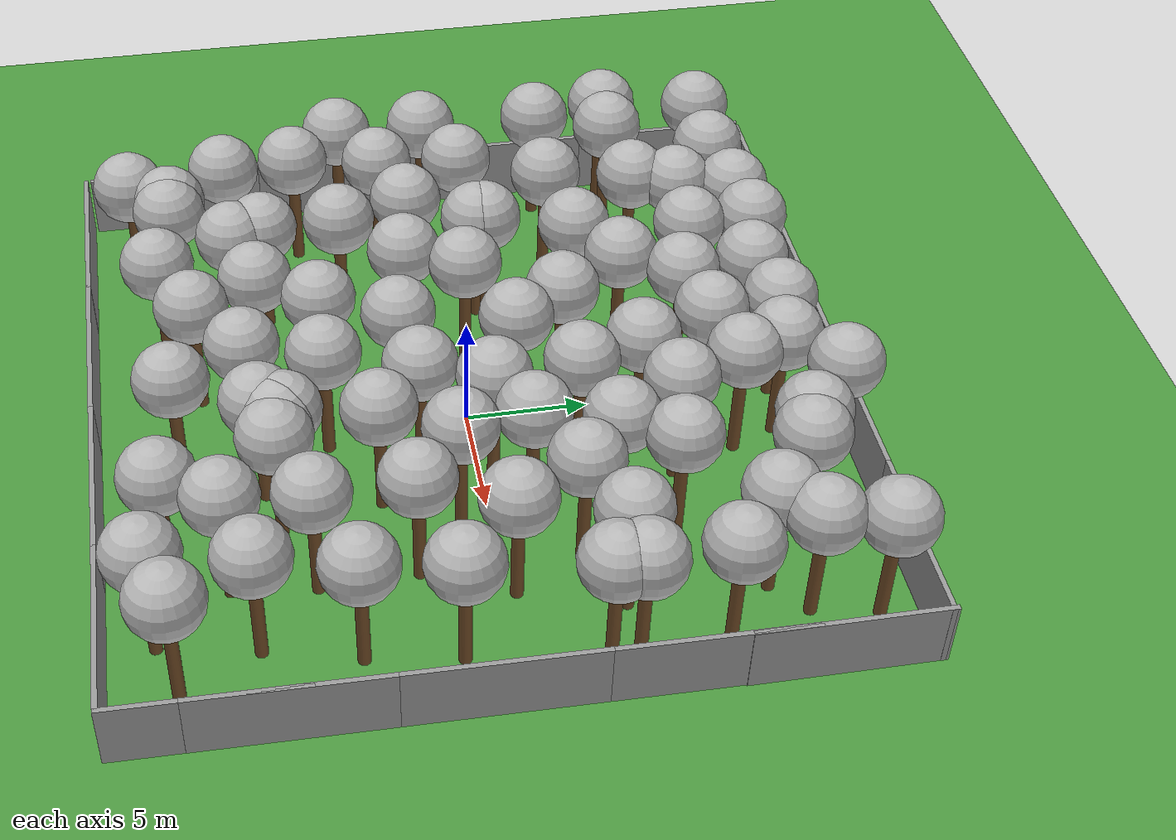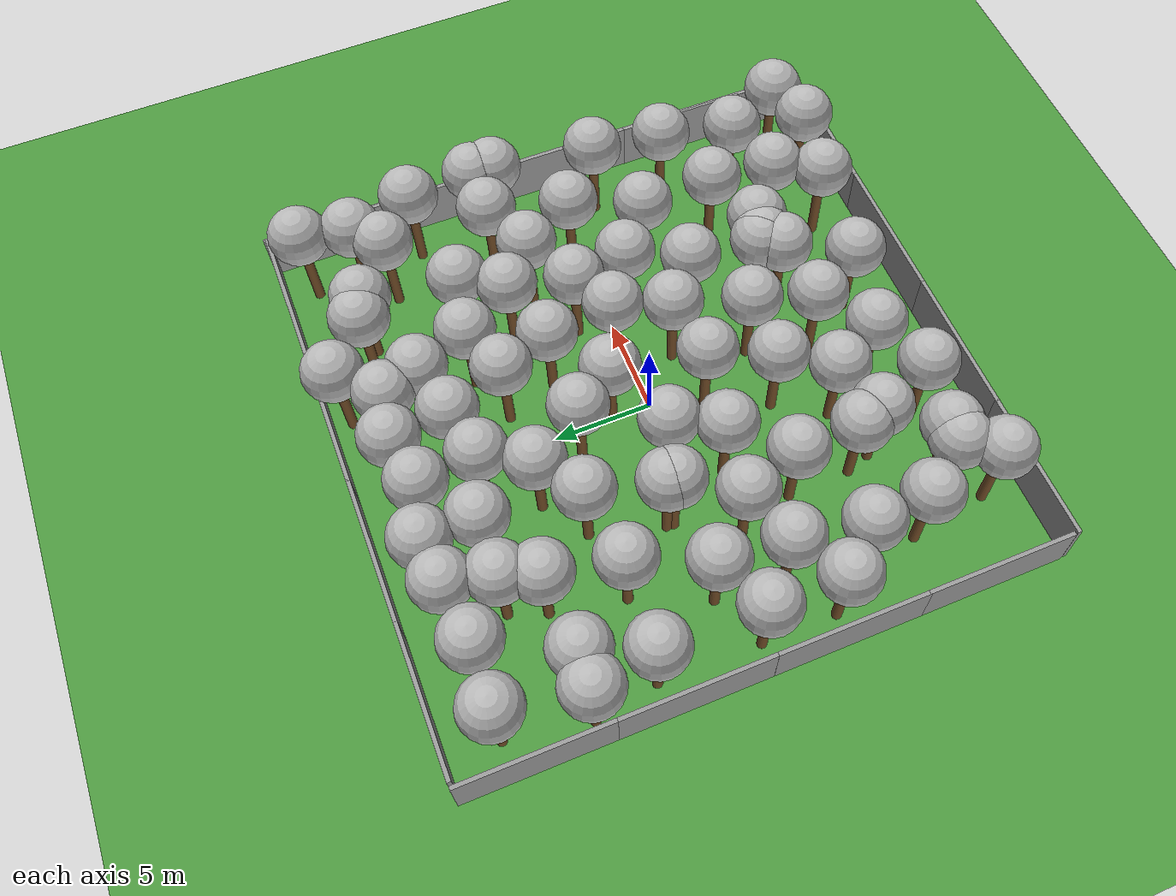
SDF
<sdf version="1.7">
 <world name="default">
  <plugin name="mrs_gazebo_static_transform_republisher_plugin" filename="libMrsGazeboCommonResources_StaticTransformRepublisher.so"/>
  <spherical_coordinates>
   <surface_model>EARTH_WGS84</surface_model>
   <latitude_deg>47.3977</latitude_deg>
   <longitude_deg>8.54559</longitude_deg>
   <elevation>0</elevation>
   <heading_deg>0</heading_deg>
  </spherical_coordinates>
  <gravity>0 0 -9.8</gravity>
  <magnetic_field>6e-06 2.3e-05 -4.2e-05</magnetic_field>
  <atmosphere type="adiabatic"/>
  <physics name="default_physics" default="0" type="ode">
   <max_step_size>0.001</max_step_size>
   <real_time_factor>1</real_time_factor>
   <real_time_update_rate>1000</real_time_update_rate>
   <ode>
    <solver>
     <type>quick</type>
     <iters>50</iters>
     <sor>1.3</sor>
     <use_dynamic_moi_rescaling>0</use_dynamic_moi_rescaling>
    </solver>
    <constraints>
     <cfm>0</cfm>
     <erp>0.2</erp>
     <contact_max_correcting_vel>10</contact_max_correcting_vel>
     <contact_surface_layer>0.001</contact_surface_layer>
    </constraints>
   </ode>
  </physics>
  <scene><shadows>0</shadows><ambient>0.4 0.4 0.4 1</ambient><background>0.7 0.7 0.7 1</background></scene>
  <light name="sun" type="directional">
   <pose>250 250 600 0 -0 0</pose>
   <diffuse>0.8 0.8 0.8 1</diffuse>
   <specular>0.2 0.2 0.2 1</specular>
   <attenuation>
    <range>1000</range>
    <constant>0.9</constant>
    <linear>0.01</linear>
    <quadratic>0.001</quadratic>
   </attenuation>
   <direction>0 0 -1</direction>
   <spot><inner_angle>0</inner_angle><outer_angle>0</outer_angle><falloff>0</falloff></spot>
  </light>
  <model name="tree_simple495">
   <static>1</static>
   <link name="link">
    <pose>0 0 0.1 0 -0 0</pose>
    <collision name="collision_trunk">
     <pose>0 0 2 0 -0 0</pose>
     <geometry><cylinder><radius>0.25</radius><length>4</length></cylinder></geometry>
    </collision>
    <collision name="collision_treetop">
     <pose>0 0 5.2 0 -0 0</pose>
     <geometry><sphere><radius>1.5</radius></sphere></geometry>
    </collision>
    <visual name="trunk">
     <pose>0 0 2 0 -0 0</pose>
     <geometry><cylinder><radius>0.25</radius><length>4</length></cylinder></geometry>
     <material>
      <script>
       <uri>model://tree_simple/scripts</uri>
       <uri>model://tree_simple/materials/textures</uri>
       <name>TreeSimple/Trunk</name>
      </script>
     </material>
    </visual>
    <visual name="treetop">
     <pose>0 0 5.2 0 -0 0</pose>
     <geometry><sphere><radius>1.5</radius></sphere></geometry>
     <material>
      <script>
       <uri>model://tree_simple/scripts</uri>
       <uri>model://tree_simple/materials/textures</uri>
       <name>TreeSimple/Treetop</name>
      </script>
     </material>
    </visual>
   </link>
   <pose>13.2663 3.23501 0 0 -0 0</pose>
  </model>
  <model name="tree_simple488">
   <static>1</static>
   <link name="link">
    <pose>0 0 0.1 0 -0 0</pose>
    <collision name="collision_trunk">
     <pose>0 0 2 0 -0 0</pose>
     <geometry><cylinder><radius>0.25</radius><length>4</length></cylinder></geometry>
    </collision>
    <collision name="collision_treetop">
     <pose>0 0 5.2 0 -0 0</pose>
     <geometry><sphere><radius>1.5</radius></sphere></geometry>
    </collision>
    <visual name="trunk">
     <pose>0 0 2 0 -0 0</pose>
     <geometry><cylinder><radius>0.25</radius><length>4</length></cylinder></geometry>
     <material>
      <script>
       <uri>model://tree_simple/scripts</uri>
       <uri>model://tree_simple/materials/textures</uri>
       <name>TreeSimple/Trunk</name>
      </script>
     </material>
    </visual>
    <visual name="treetop">
     <pose>0 0 5.2 0 -0 0</pose>
     <geometry><sphere><radius>1.5</radius></sphere></geometry>
     <material>
      <script>
       <uri>model://tree_simple/scripts</uri>
       <uri>model://tree_simple/materials/textures</uri>
       <name>TreeSimple/Treetop</name>
      </script>
     </material>
    </visual>
   </link>
   <pose>-13.1216 12.436 0 0 -0 0</pose>
  </model>
  <model name="tree_simple486">
   <static>1</static>
   <link name="link">
    <pose>0 0 0.1 0 -0 0</pose>
    <collision name="collision_trunk">
     <pose>0 0 2 0 -0 0</pose>
     <geometry><cylinder><radius>0.25</radius><length>4</length></cylinder></geometry>
    </collision>
    <collision name="collision_treetop">
     <pose>0 0 5.2 0 -0 0</pose>
     <geometry><sphere><radius>1.5</radius></sphere></geometry>
    </collision>
    <visual name="trunk">
     <pose>0 0 2 0 -0 0</pose>
     <geometry><cylinder><radius>0.25</radius><length>4</length></cylinder></geometry>
     <material>
      <script>
       <uri>model://tree_simple/scripts</uri>
       <uri>model://tree_simple/materials/textures</uri>
       <name>TreeSimple/Trunk</name>
      </script>
     </material>
    </visual>
    <visual name="treetop">
     <pose>0 0 5.2 0 -0 0</pose>
     <geometry><sphere><radius>1.5</radius></sphere></geometry>
     <material>
      <script>
       <uri>model://tree_simple/scripts</uri>
       <uri>model://tree_simple/materials/textures</uri>
       <name>TreeSimple/Treetop</name>
      </script>
     </material>
    </visual>
   </link>
   <pose>8.18282 11.6524 0 0 -0 0</pose>
  </model>
  <model name="tree_simple480">
   <static>1</static>
   <link name="link">
    <pose>0 0 0.1 0 -0 0</pose>
    <collision name="collision_trunk">
     <pose>0 0 2 0 -0 0</pose>
     <geometry><cylinder><radius>0.25</radius><length>4</length></cylinder></geometry>
    </collision>
    <collision name="collision_treetop">
     <pose>0 0 5.2 0 -0 0</pose>
     <geometry><sphere><radius>1.5</radius></sphere></geometry>
    </collision>
    <visual name="trunk">
     <pose>0 0 2 0 -0 0</pose>
     <geometry><cylinder><radius>0.25</radius><length>4</length></cylinder></geometry>
     <material>
      <script>
       <uri>model://tree_simple/scripts</uri>
       <uri>model://tree_simple/materials/textures</uri>
       <name>TreeSimple/Trunk</name>
      </script>
     </material>
    </visual>
    <visual name="treetop">
     <pose>0 0 5.2 0 -0 0</pose>
     <geometry><sphere><radius>1.5</radius></sphere></geometry>
     <material>
      <script>
       <uri>model://tree_simple/scripts</uri>
       <uri>model://tree_simple/materials/textures</uri>
       <name>TreeSimple/Treetop</name>
      </script>
     </material>
    </visual>
   </link>
   <pose>-2.16211 12.1351 0 0 -0 0</pose>
  </model>
  <model name="tree_simple478">
   <static>1</static>
   <link name="link">
    <pose>0 0 0.1 0 -0 0</pose>
    <collision name="collision_trunk">
     <pose>0 0 2 0 -0 0</pose>
     <geometry><cylinder><radius>0.25</radius><length>4</length></cylinder></geometry>
    </collision>
    <collision name="collision_treetop">
     <pose>0 0 5.2 0 -0 0</pose>
     <geometry><sphere><radius>1.5</radius></sphere></geometry>
    </collision>
    <visual name="trunk">
     <pose>0 0 2 0 -0 0</pose>
     <geometry><cylinder><radius>0.25</radius><length>4</length></cylinder></geometry>
     <material>
      <script>
       <uri>model://tree_simple/scripts</uri>
       <uri>model://tree_simple/materials/textures</uri>
       <name>TreeSimple/Trunk</name>
      </script>
     </material>
    </visual>
    <visual name="treetop">
     <pose>0 0 5.2 0 -0 0</pose>
     <geometry><sphere><radius>1.5</radius></sphere></geometry>
     <material>
      <script>
       <uri>model://tree_simple/scripts</uri>
       <uri>model://tree_simple/materials/textures</uri>
       <name>TreeSimple/Treetop</name>
      </script>
     </material>
    </visual>
   </link>
   <pose>6.74093 -12.3163 0 0 -0 0</pose>
  </model>
  <model name="tree_simple463">
   <static>1</static>
   <link name="link">
    <pose>0 0 0.1 0 -0 0</pose>
    <collision name="collision_trunk">
     <pose>0 0 2 0 -0 0</pose>
     <geometry><cylinder><radius>0.25</radius><length>4</length></cylinder></geometry>
    </collision>
    <collision name="collision_treetop">
     <pose>0 0 5.2 0 -0 0</pose>
     <geometry><sphere><radius>1.5</radius></sphere></geometry>
    </collision>
    <visual name="trunk">
     <pose>0 0 2 0 -0 0</pose>
     <geometry><cylinder><radius>0.25</radius><length>4</length></cylinder></geometry>
     <material>
      <script>
       <uri>model://tree_simple/scripts</uri>
       <uri>model://tree_simple/materials/textures</uri>
       <name>TreeSimple/Trunk</name>
      </script>
     </material>
    </visual>
    <visual name="treetop">
     <pose>0 0 5.2 0 -0 0</pose>
     <geometry><sphere><radius>1.5</radius></sphere></geometry>
     <material>
      <script>
       <uri>model://tree_simple/scripts</uri>
       <uri>model://tree_simple/materials/textures</uri>
       <name>TreeSimple/Treetop</name>
      </script>
     </material>
    </visual>
   </link>
   <pose>4.14453 -7.71734 0 0 -0 0</pose>
  </model>
  <model name="tree_simple453">
   <static>1</static>
   <link name="link">
    <pose>0 0 0.1 0 -0 0</pose>
    <collision name="collision_trunk">
     <pose>0 0 2 0 -0 0</pose>
     <geometry><cylinder><radius>0.25</radius><length>4</length></cylinder></geometry>
    </collision>
    <collision name="collision_treetop">
     <pose>0 0 5.2 0 -0 0</pose>
     <geometry><sphere><radius>1.5</radius></sphere></geometry>
    </collision>
    <visual name="trunk">
     <pose>0 0 2 0 -0 0</pose>
     <geometry><cylinder><radius>0.25</radius><length>4</length></cylinder></geometry>
     <material>
      <script>
       <uri>model://tree_simple/scripts</uri>
       <uri>model://tree_simple/materials/textures</uri>
       <name>TreeSimple/Trunk</name>
      </script>
     </material>
    </visual>
    <visual name="treetop">
     <pose>0 0 5.2 0 -0 0</pose>
     <geometry><sphere><radius>1.5</radius></sphere></geometry>
     <material>
      <script>
       <uri>model://tree_simple/scripts</uri>
       <uri>model://tree_simple/materials/textures</uri>
       <name>TreeSimple/Treetop</name>
      </script>
     </material>
    </visual>
   </link>
   <pose>-12.1353 8.19022 0 0 -0 0</pose>
  </model>
  <model name="tree_simple432">
   <static>1</static>
   <link name="link">
    <pose>0 0 0.1 0 -0 0</pose>
    <collision name="collision_trunk">
     <pose>0 0 2 0 -0 0</pose>
     <geometry><cylinder><radius>0.25</radius><length>4</length></cylinder></geometry>
    </collision>
    <collision name="collision_treetop">
     <pose>0 0 5.2 0 -0 0</pose>
     <geometry><sphere><radius>1.5</radius></sphere></geometry>
    </collision>
    <visual name="trunk">
     <pose>0 0 2 0 -0 0</pose>
     <geometry><cylinder><radius>0.25</radius><length>4</length></cylinder></geometry>
     <material>
      <script>
       <uri>model://tree_simple/scripts</uri>
       <uri>model://tree_simple/materials/textures</uri>
       <name>TreeSimple/Trunk</name>
      </script>
     </material>
    </visual>
    <visual name="treetop">
     <pose>0 0 5.2 0 -0 0</pose>
     <geometry><sphere><radius>1.5</radius></sphere></geometry>
     <material>
      <script>
       <uri>model://tree_simple/scripts</uri>
       <uri>model://tree_simple/materials/textures</uri>
       <name>TreeSimple/Treetop</name>
      </script>
     </material>
    </visual>
   </link>
   <pose>8.39658 -6.88849 0 0 -0 0</pose>
  </model>
  <model name="tree_simple421">
   <static>1</static>
   <link name="link">
    <pose>0 0 0.1 0 -0 0</pose>
    <collision name="collision_trunk">
     <pose>0 0 2 0 -0 0</pose>
     <geometry><cylinder><radius>0.25</radius><length>4</length></cylinder></geometry>
    </collision>
    <collision name="collision_treetop">
     <pose>0 0 5.2 0 -0 0</pose>
     <geometry><sphere><radius>1.5</radius></sphere></geometry>
    </collision>
    <visual name="trunk">
     <pose>0 0 2 0 -0 0</pose>
     <geometry><cylinder><radius>0.25</radius><length>4</length></cylinder></geometry>
     <material>
      <script>
       <uri>model://tree_simple/scripts</uri>
       <uri>model://tree_simple/materials/textures</uri>
       <name>TreeSimple/Trunk</name>
      </script>
     </material>
    </visual>
    <visual name="treetop">
     <pose>0 0 5.2 0 -0 0</pose>
     <geometry><sphere><radius>1.5</radius></sphere></geometry>
     <material>
      <script>
       <uri>model://tree_simple/scripts</uri>
       <uri>model://tree_simple/materials/textures</uri>
       <name>TreeSimple/Treetop</name>
      </script>
     </material>
    </visual>
   </link>
   <pose>7.02493 12.056 0 0 -0 0</pose>
  </model>
  <model name="tree_simple417">
   <static>1</static>
   <link name="link">
    <pose>0 0 0.1 0 -0 0</pose>
    <collision name="collision_trunk">
     <pose>0 0 2 0 -0 0</pose>
     <geometry><cylinder><radius>0.25</radius><length>4</length></cylinder></geometry>
    </collision>
    <collision name="collision_treetop">
     <pose>0 0 5.2 0 -0 0</pose>
     <geometry><sphere><radius>1.5</radius></sphere></geometry>
    </collision>
    <visual name="trunk">
     <pose>0 0 2 0 -0 0</pose>
     <geometry><cylinder><radius>0.25</radius><length>4</length></cylinder></geometry>
     <material>
      <script>
       <uri>model://tree_simple/scripts</uri>
       <uri>model://tree_simple/materials/textures</uri>
       <name>TreeSimple/Trunk</name>
      </script>
     </material>
    </visual>
    <visual name="treetop">
     <pose>0 0 5.2 0 -0 0</pose>
     <geometry><sphere><radius>1.5</radius></sphere></geometry>
     <material>
      <script>
       <uri>model://tree_simple/scripts</uri>
       <uri>model://tree_simple/materials/textures</uri>
       <name>TreeSimple/Treetop</name>
      </script>
     </material>
    </visual>
   </link>
   <pose>-1.82311 9.17527 0 0 -0 0</pose>
  </model>
  <model name="tree_simple415">
   <static>1</static>
   <link name="link">
    <pose>0 0 0.1 0 -0 0</pose>
    <collision name="collision_trunk">
     <pose>0 0 2 0 -0 0</pose>
     <geometry><cylinder><radius>0.25</radius><length>4</length></cylinder></geometry>
    </collision>
    <collision name="collision_treetop">
     <pose>0 0 5.2 0 -0 0</pose>
     <geometry><sphere><radius>1.5</radius></sphere></geometry>
    </collision>
    <visual name="trunk">
     <pose>0 0 2 0 -0 0</pose>
     <geometry><cylinder><radius>0.25</radius><length>4</length></cylinder></geometry>
     <material>
      <script>
       <uri>model://tree_simple/scripts</uri>
       <uri>model://tree_simple/materials/textures</uri>
       <name>TreeSimple/Trunk</name>
      </script>
     </material>
    </visual>
    <visual name="treetop">
     <pose>0 0 5.2 0 -0 0</pose>
     <geometry><sphere><radius>1.5</radius></sphere></geometry>
     <material>
      <script>
       <uri>model://tree_simple/scripts</uri>
       <uri>model://tree_simple/materials/textures</uri>
       <name>TreeSimple/Treetop</name>
      </script>
     </material>
    </visual>
   </link>
   <pose>-11.6356 -5.82525 0 0 -0 0</pose>
  </model>
  <model name="tree_simple412">
   <static>1</static>
   <link name="link">
    <pose>0 0 0.1 0 -0 0</pose>
    <collision name="collision_trunk">
     <pose>0 0 2 0 -0 0</pose>
     <geometry><cylinder><radius>0.25</radius><length>4</length></cylinder></geometry>
    </collision>
    <collision name="collision_treetop">
     <pose>0 0 5.2 0 -0 0</pose>
     <geometry><sphere><radius>1.5</radius></sphere></geometry>
    </collision>
    <visual name="trunk">
     <pose>0 0 2 0 -0 0</pose>
     <geometry><cylinder><radius>0.25</radius><length>4</length></cylinder></geometry>
     <material>
      <script>
       <uri>model://tree_simple/scripts</uri>
       <uri>model://tree_simple/materials/textures</uri>
       <name>TreeSimple/Trunk</name>
      </script>
     </material>
    </visual>
    <visual name="treetop">
     <pose>0 0 5.2 0 -0 0</pose>
     <geometry><sphere><radius>1.5</radius></sphere></geometry>
     <material>
      <script>
       <uri>model://tree_simple/scripts</uri>
       <uri>model://tree_simple/materials/textures</uri>
       <name>TreeSimple/Treetop</name>
      </script>
     </material>
    </visual>
   </link>
   <pose>1.94235 6.68973 0 0 -0 0</pose>
  </model>
  <model name="tree_simple392">
   <static>1</static>
   <link name="link">
    <pose>0 0 0.1 0 -0 0</pose>
    <collision name="collision_trunk">
     <pose>0 0 2 0 -0 0</pose>
     <geometry><cylinder><radius>0.25</radius><length>4</length></cylinder></geometry>
    </collision>
    <collision name="collision_treetop">
     <pose>0 0 5.2 0 -0 0</pose>
     <geometry><sphere><radius>1.5</radius></sphere></geometry>
    </collision>
    <visual name="trunk">
     <pose>0 0 2 0 -0 0</pose>
     <geometry><cylinder><radius>0.25</radius><length>4</length></cylinder></geometry>
     <material>
      <script>
       <uri>model://tree_simple/scripts</uri>
       <uri>model://tree_simple/materials/textures</uri>
       <name>TreeSimple/Trunk</name>
      </script>
     </material>
    </visual>
    <visual name="treetop">
     <pose>0 0 5.2 0 -0 0</pose>
     <geometry><sphere><radius>1.5</radius></sphere></geometry>
     <material>
      <script>
       <uri>model://tree_simple/scripts</uri>
       <uri>model://tree_simple/materials/textures</uri>
       <name>TreeSimple/Treetop</name>
      </script>
     </material>
    </visual>
   </link>
   <pose>-2.49228 -10.6348 0 0 -0 0</pose>
  </model>
  <model name="tree_simple389">
   <static>1</static>
   <link name="link">
    <pose>0 0 0.1 0 -0 0</pose>
    <collision name="collision_trunk">
     <pose>0 0 2 0 -0 0</pose>
     <geometry><cylinder><radius>0.25</radius><length>4</length></cylinder></geometry>
    </collision>
    <collision name="collision_treetop">
     <pose>0 0 5.2 0 -0 0</pose>
     <geometry><sphere><radius>1.5</radius></sphere></geometry>
    </collision>
    <visual name="trunk">
     <pose>0 0 2 0 -0 0</pose>
     <geometry><cylinder><radius>0.25</radius><length>4</length></cylinder></geometry>
     <material>
      <script>
       <uri>model://tree_simple/scripts</uri>
       <uri>model://tree_simple/materials/textures</uri>
       <name>TreeSimple/Trunk</name>
      </script>
     </material>
    </visual>
    <visual name="treetop">
     <pose>0 0 5.2 0 -0 0</pose>
     <geometry><sphere><radius>1.5</radius></sphere></geometry>
     <material>
      <script>
       <uri>model://tree_simple/scripts</uri>
       <uri>model://tree_simple/materials/textures</uri>
       <name>TreeSimple/Treetop</name>
      </script>
     </material>
    </visual>
   </link>
   <pose>12.5934 -12.2598 0 0 -0 0</pose>
  </model>
  <model name="tree_simple376">
   <static>1</static>
   <link name="link">
    <pose>0 0 0.1 0 -0 0</pose>
    <collision name="collision_trunk">
     <pose>0 0 2 0 -0 0</pose>
     <geometry><cylinder><radius>0.25</radius><length>4</length></cylinder></geometry>
    </collision>
    <collision name="collision_treetop">
     <pose>0 0 5.2 0 -0 0</pose>
     <geometry><sphere><radius>1.5</radius></sphere></geometry>
    </collision>
    <visual name="trunk">
     <pose>0 0 2 0 -0 0</pose>
     <geometry><cylinder><radius>0.25</radius><length>4</length></cylinder></geometry>
     <material>
      <script>
       <uri>model://tree_simple/scripts</uri>
       <uri>model://tree_simple/materials/textures</uri>
       <name>TreeSimple/Trunk</name>
      </script>
     </material>
    </visual>
    <visual name="treetop">
     <pose>0 0 5.2 0 -0 0</pose>
     <geometry><sphere><radius>1.5</radius></sphere></geometry>
     <material>
      <script>
       <uri>model://tree_simple/scripts</uri>
       <uri>model://tree_simple/materials/textures</uri>
       <name>TreeSimple/Treetop</name>
      </script>
     </material>
    </visual>
   </link>
   <pose>-3.57496 0.511559 0 0 -0 0</pose>
  </model>
  <model name="tree_simple360">
   <static>1</static>
   <link name="link">
    <pose>0 0 0.1 0 -0 0</pose>
    <collision name="collision_trunk">
     <pose>0 0 2 0 -0 0</pose>
     <geometry><cylinder><radius>0.25</radius><length>4</length></cylinder></geometry>
    </collision>
    <collision name="collision_treetop">
     <pose>0 0 5.2 0 -0 0</pose>
     <geometry><sphere><radius>1.5</radius></sphere></geometry>
    </collision>
    <visual name="trunk">
     <pose>0 0 2 0 -0 0</pose>
     <geometry><cylinder><radius>0.25</radius><length>4</length></cylinder></geometry>
     <material>
      <script>
       <uri>model://tree_simple/scripts</uri>
       <uri>model://tree_simple/materials/textures</uri>
       <name>TreeSimple/Trunk</name>
      </script>
     </material>
    </visual>
    <visual name="treetop">
     <pose>0 0 5.2 0 -0 0</pose>
     <geometry><sphere><radius>1.5</radius></sphere></geometry>
     <material>
      <script>
       <uri>model://tree_simple/scripts</uri>
       <uri>model://tree_simple/materials/textures</uri>
       <name>TreeSimple/Treetop</name>
      </script>
     </material>
    </visual>
   </link>
   <pose>-13.8762 8.30703 0 0 -0 0</pose>
  </model>
  <model name="tree_simple350">
   <static>1</static>
   <link name="link">
    <pose>0 0 0.1 0 -0 0</pose>
    <collision name="collision_trunk">
     <pose>0 0 2 0 -0 0</pose>
     <geometry><cylinder><radius>0.25</radius><length>4</length></cylinder></geometry>
    </collision>
    <collision name="collision_treetop">
     <pose>0 0 5.2 0 -0 0</pose>
     <geometry><sphere><radius>1.5</radius></sphere></geometry>
    </collision>
    <visual name="trunk">
     <pose>0 0 2 0 -0 0</pose>
     <geometry><cylinder><radius>0.25</radius><length>4</length></cylinder></geometry>
     <material>
      <script>
       <uri>model://tree_simple/scripts</uri>
       <uri>model://tree_simple/materials/textures</uri>
       <name>TreeSimple/Trunk</name>
      </script>
     </material>
    </visual>
    <visual name="treetop">
     <pose>0 0 5.2 0 -0 0</pose>
     <geometry><sphere><radius>1.5</radius></sphere></geometry>
     <material>
      <script>
       <uri>model://tree_simple/scripts</uri>
       <uri>model://tree_simple/materials/textures</uri>
       <name>TreeSimple/Treetop</name>
      </script>
     </material>
    </visual>
   </link>
   <pose>5.40258 1.73801 0 0 -0 0</pose>
  </model>
  <model name="tree_simple346">
   <static>1</static>
   <link name="link">
    <pose>0 0 0.1 0 -0 0</pose>
    <collision name="collision_trunk">
     <pose>0 0 2 0 -0 0</pose>
     <geometry><cylinder><radius>0.25</radius><length>4</length></cylinder></geometry>
    </collision>
    <collision name="collision_treetop">
     <pose>0 0 5.2 0 -0 0</pose>
     <geometry><sphere><radius>1.5</radius></sphere></geometry>
    </collision>
    <visual name="trunk">
     <pose>0 0 2 0 -0 0</pose>
     <geometry><cylinder><radius>0.25</radius><length>4</length></cylinder></geometry>
     <material>
      <script>
       <uri>model://tree_simple/scripts</uri>
       <uri>model://tree_simple/materials/textures</uri>
       <name>TreeSimple/Trunk</name>
      </script>
     </material>
    </visual>
    <visual name="treetop">
     <pose>0 0 5.2 0 -0 0</pose>
     <geometry><sphere><radius>1.5</radius></sphere></geometry>
     <material>
      <script>
       <uri>model://tree_simple/scripts</uri>
       <uri>model://tree_simple/materials/textures</uri>
       <name>TreeSimple/Treetop</name>
      </script>
     </material>
    </visual>
   </link>
   <pose>6.18559 4.9134 0 0 -0 0</pose>
  </model>
  <model name="tree_simple324">
   <static>1</static>
   <link name="link">
    <pose>0 0 0.1 0 -0 0</pose>
    <collision name="collision_trunk">
     <pose>0 0 2 0 -0 0</pose>
     <geometry><cylinder><radius>0.25</radius><length>4</length></cylinder></geometry>
    </collision>
    <collision name="collision_treetop">
     <pose>0 0 5.2 0 -0 0</pose>
     <geometry><sphere><radius>1.5</radius></sphere></geometry>
    </collision>
    <visual name="trunk">
     <pose>0 0 2 0 -0 0</pose>
     <geometry><cylinder><radius>0.25</radius><length>4</length></cylinder></geometry>
     <material>
      <script>
       <uri>model://tree_simple/scripts</uri>
       <uri>model://tree_simple/materials/textures</uri>
       <name>TreeSimple/Trunk</name>
      </script>
     </material>
    </visual>
    <visual name="treetop">
     <pose>0 0 5.2 0 -0 0</pose>
     <geometry><sphere><radius>1.5</radius></sphere></geometry>
     <material>
      <script>
       <uri>model://tree_simple/scripts</uri>
       <uri>model://tree_simple/materials/textures</uri>
       <name>TreeSimple/Treetop</name>
      </script>
     </material>
    </visual>
   </link>
   <pose>2.67974 12.1657 0 0 -0 0</pose>
  </model>
  <model name="tree_simple322">
   <static>1</static>
   <link name="link">
    <pose>0 0 0.1 0 -0 0</pose>
    <collision name="collision_trunk">
     <pose>0 0 2 0 -0 0</pose>
     <geometry><cylinder><radius>0.25</radius><length>4</length></cylinder></geometry>
    </collision>
    <collision name="collision_treetop">
     <pose>0 0 5.2 0 -0 0</pose>
     <geometry><sphere><radius>1.5</radius></sphere></geometry>
    </collision>
    <visual name="trunk">
     <pose>0 0 2 0 -0 0</pose>
     <geometry><cylinder><radius>0.25</radius><length>4</length></cylinder></geometry>
     <material>
      <script>
       <uri>model://tree_simple/scripts</uri>
       <uri>model://tree_simple/materials/textures</uri>
       <name>TreeSimple/Trunk</name>
      </script>
     </material>
    </visual>
    <visual name="treetop">
     <pose>0 0 5.2 0 -0 0</pose>
     <geometry><sphere><radius>1.5</radius></sphere></geometry>
     <material>
      <script>
       <uri>model://tree_simple/scripts</uri>
       <uri>model://tree_simple/materials/textures</uri>
       <name>TreeSimple/Treetop</name>
      </script>
     </material>
    </visual>
   </link>
   <pose>-10.7837 -12.8599 0 0 -0 0</pose>
  </model>
  <model name="tree_simple308">
   <static>1</static>
   <link name="link">
    <pose>0 0 0.1 0 -0 0</pose>
    <collision name="collision_trunk">
     <pose>0 0 2 0 -0 0</pose>
     <geometry><cylinder><radius>0.25</radius><length>4</length></cylinder></geometry>
    </collision>
    <collision name="collision_treetop">
     <pose>0 0 5.2 0 -0 0</pose>
     <geometry><sphere><radius>1.5</radius></sphere></geometry>
    </collision>
    <visual name="trunk">
     <pose>0 0 2 0 -0 0</pose>
     <geometry><cylinder><radius>0.25</radius><length>4</length></cylinder></geometry>
     <material>
      <script>
       <uri>model://tree_simple/scripts</uri>
       <uri>model://tree_simple/materials/textures</uri>
       <name>TreeSimple/Trunk</name>
      </script>
     </material>
    </visual>
    <visual name="treetop">
     <pose>0 0 5.2 0 -0 0</pose>
     <geometry><sphere><radius>1.5</radius></sphere></geometry>
     <material>
      <script>
       <uri>model://tree_simple/scripts</uri>
       <uri>model://tree_simple/materials/textures</uri>
       <name>TreeSimple/Treetop</name>
      </script>
     </material>
    </visual>
   </link>
   <pose>3.23733 0.582979 0 0 -0 0</pose>
  </model>
  <model name="tree_simple304">
   <static>1</static>
   <link name="link">
    <pose>0 0 0.1 0 -0 0</pose>
    <collision name="collision_trunk">
     <pose>0 0 2 0 -0 0</pose>
     <geometry><cylinder><radius>0.25</radius><length>4</length></cylinder></geometry>
    </collision>
    <collision name="collision_treetop">
     <pose>0 0 5.2 0 -0 0</pose>
     <geometry><sphere><radius>1.5</radius></sphere></geometry>
    </collision>
    <visual name="trunk">
     <pose>0 0 2 0 -0 0</pose>
     <geometry><cylinder><radius>0.25</radius><length>4</length></cylinder></geometry>
     <material>
      <script>
       <uri>model://tree_simple/scripts</uri>
       <uri>model://tree_simple/materials/textures</uri>
       <name>TreeSimple/Trunk</name>
      </script>
     </material>
    </visual>
    <visual name="treetop">
     <pose>0 0 5.2 0 -0 0</pose>
     <geometry><sphere><radius>1.5</radius></sphere></geometry>
     <material>
      <script>
       <uri>model://tree_simple/scripts</uri>
       <uri>model://tree_simple/materials/textures</uri>
       <name>TreeSimple/Treetop</name>
      </script>
     </material>
    </visual>
   </link>
   <pose>12.7492 13.4737 0 0 -0 0</pose>
  </model>
  <model name="tree_simple303">
   <static>1</static>
   <link name="link">
    <pose>0 0 0.1 0 -0 0</pose>
    <collision name="collision_trunk">
     <pose>0 0 2 0 -0 0</pose>
     <geometry><cylinder><radius>0.25</radius><length>4</length></cylinder></geometry>
    </collision>
    <collision name="collision_treetop">
     <pose>0 0 5.2 0 -0 0</pose>
     <geometry><sphere><radius>1.5</radius></sphere></geometry>
    </collision>
    <visual name="trunk">
     <pose>0 0 2 0 -0 0</pose>
     <geometry><cylinder><radius>0.25</radius><length>4</length></cylinder></geometry>
     <material>
      <script>
       <uri>model://tree_simple/scripts</uri>
       <uri>model://tree_simple/materials/textures</uri>
       <name>TreeSimple/Trunk</name>
      </script>
     </material>
    </visual>
    <visual name="treetop">
     <pose>0 0 5.2 0 -0 0</pose>
     <geometry><sphere><radius>1.5</radius></sphere></geometry>
     <material>
      <script>
       <uri>model://tree_simple/scripts</uri>
       <uri>model://tree_simple/materials/textures</uri>
       <name>TreeSimple/Treetop</name>
      </script>
     </material>
    </visual>
   </link>
   <pose>-9.56095 -11.2139 0 0 -0 0</pose>
  </model>
  <model name="tree_simple269">
   <static>1</static>
   <link name="link">
    <pose>0 0 0.1 0 -0 0</pose>
    <collision name="collision_trunk">
     <pose>0 0 2 0 -0 0</pose>
     <geometry><cylinder><radius>0.25</radius><length>4</length></cylinder></geometry>
    </collision>
    <collision name="collision_treetop">
     <pose>0 0 5.2 0 -0 0</pose>
     <geometry><sphere><radius>1.5</radius></sphere></geometry>
    </collision>
    <visual name="trunk">
     <pose>0 0 2 0 -0 0</pose>
     <geometry><cylinder><radius>0.25</radius><length>4</length></cylinder></geometry>
     <material>
      <script>
       <uri>model://tree_simple/scripts</uri>
       <uri>model://tree_simple/materials/textures</uri>
       <name>TreeSimple/Trunk</name>
      </script>
     </material>
    </visual>
    <visual name="treetop">
     <pose>0 0 5.2 0 -0 0</pose>
     <geometry><sphere><radius>1.5</radius></sphere></geometry>
     <material>
      <script>
       <uri>model://tree_simple/scripts</uri>
       <uri>model://tree_simple/materials/textures</uri>
       <name>TreeSimple/Treetop</name>
      </script>
     </material>
    </visual>
   </link>
   <pose>3.43166 10.3419 0 0 -0 0</pose>
  </model>
  <model name="tree_simple253">
   <static>1</static>
   <link name="link">
    <pose>0 0 0.1 0 -0 0</pose>
    <collision name="collision_trunk">
     <pose>0 0 2 0 -0 0</pose>
     <geometry><cylinder><radius>0.25</radius><length>4</length></cylinder></geometry>
    </collision>
    <collision name="collision_treetop">
     <pose>0 0 5.2 0 -0 0</pose>
     <geometry><sphere><radius>1.5</radius></sphere></geometry>
    </collision>
    <visual name="trunk">
     <pose>0 0 2 0 -0 0</pose>
     <geometry><cylinder><radius>0.25</radius><length>4</length></cylinder></geometry>
     <material>
      <script>
       <uri>model://tree_simple/scripts</uri>
       <uri>model://tree_simple/materials/textures</uri>
       <name>TreeSimple/Trunk</name>
      </script>
     </material>
    </visual>
    <visual name="treetop">
     <pose>0 0 5.2 0 -0 0</pose>
     <geometry><sphere><radius>1.5</radius></sphere></geometry>
     <material>
      <script>
       <uri>model://tree_simple/scripts</uri>
       <uri>model://tree_simple/materials/textures</uri>
       <name>TreeSimple/Treetop</name>
      </script>
     </material>
    </visual>
   </link>
   <pose>-6.71888 -8.75374 0 0 -0 0</pose>
  </model>
  <model name="tree_simple246">
   <static>1</static>
   <link name="link">
    <pose>0 0 0.1 0 -0 0</pose>
    <collision name="collision_trunk">
     <pose>0 0 2 0 -0 0</pose>
     <geometry><cylinder><radius>0.25</radius><length>4</length></cylinder></geometry>
    </collision>
    <collision name="collision_treetop">
     <pose>0 0 5.2 0 -0 0</pose>
     <geometry><sphere><radius>1.5</radius></sphere></geometry>
    </collision>
    <visual name="trunk">
     <pose>0 0 2 0 -0 0</pose>
     <geometry><cylinder><radius>0.25</radius><length>4</length></cylinder></geometry>
     <material>
      <script>
       <uri>model://tree_simple/scripts</uri>
       <uri>model://tree_simple/materials/textures</uri>
       <name>TreeSimple/Trunk</name>
      </script>
     </material>
    </visual>
    <visual name="treetop">
     <pose>0 0 5.2 0 -0 0</pose>
     <geometry><sphere><radius>1.5</radius></sphere></geometry>
     <material>
      <script>
       <uri>model://tree_simple/scripts</uri>
       <uri>model://tree_simple/materials/textures</uri>
       <name>TreeSimple/Treetop</name>
      </script>
     </material>
    </visual>
   </link>
   <pose>4.59531 14.0378 0 0 -0 0</pose>
  </model>
  <model name="tree_simple234">
   <static>1</static>
   <link name="link">
    <pose>0 0 0.1 0 -0 0</pose>
    <collision name="collision_trunk">
     <pose>0 0 2 0 -0 0</pose>
     <geometry><cylinder><radius>0.25</radius><length>4</length></cylinder></geometry>
    </collision>
    <collision name="collision_treetop">
     <pose>0 0 5.2 0 -0 0</pose>
     <geometry><sphere><radius>1.5</radius></sphere></geometry>
    </collision>
    <visual name="trunk">
     <pose>0 0 2 0 -0 0</pose>
     <geometry><cylinder><radius>0.25</radius><length>4</length></cylinder></geometry>
     <material>
      <script>
       <uri>model://tree_simple/scripts</uri>
       <uri>model://tree_simple/materials/textures</uri>
       <name>TreeSimple/Trunk</name>
      </script>
     </material>
    </visual>
    <visual name="treetop">
     <pose>0 0 5.2 0 -0 0</pose>
     <geometry><sphere><radius>1.5</radius></sphere></geometry>
     <material>
      <script>
       <uri>model://tree_simple/scripts</uri>
       <uri>model://tree_simple/materials/textures</uri>
       <name>TreeSimple/Treetop</name>
      </script>
     </material>
    </visual>
   </link>
   <pose>-7.13672 -7.51189 0 0 -0 0</pose>
  </model>
  <model name="tree_simple222">
   <static>1</static>
   <link name="link">
    <pose>0 0 0.1 0 -0 0</pose>
    <collision name="collision_trunk">
     <pose>0 0 2 0 -0 0</pose>
     <geometry><cylinder><radius>0.25</radius><length>4</length></cylinder></geometry>
    </collision>
    <collision name="collision_treetop">
     <pose>0 0 5.2 0 -0 0</pose>
     <geometry><sphere><radius>1.5</radius></sphere></geometry>
    </collision>
    <visual name="trunk">
     <pose>0 0 2 0 -0 0</pose>
     <geometry><cylinder><radius>0.25</radius><length>4</length></cylinder></geometry>
     <material>
      <script>
       <uri>model://tree_simple/scripts</uri>
       <uri>model://tree_simple/materials/textures</uri>
       <name>TreeSimple/Trunk</name>
      </script>
     </material>
    </visual>
    <visual name="treetop">
     <pose>0 0 5.2 0 -0 0</pose>
     <geometry><sphere><radius>1.5</radius></sphere></geometry>
     <material>
      <script>
       <uri>model://tree_simple/scripts</uri>
       <uri>model://tree_simple/materials/textures</uri>
       <name>TreeSimple/Treetop</name>
      </script>
     </material>
    </visual>
   </link>
   <pose>3.92505 -7.51224 0 0 -0 0</pose>
  </model>
  <model name="tree_simple187">
   <static>1</static>
   <link name="link">
    <pose>0 0 0.1 0 -0 0</pose>
    <collision name="collision_trunk">
     <pose>0 0 2 0 -0 0</pose>
     <geometry><cylinder><radius>0.25</radius><length>4</length></cylinder></geometry>
    </collision>
    <collision name="collision_treetop">
     <pose>0 0 5.2 0 -0 0</pose>
     <geometry><sphere><radius>1.5</radius></sphere></geometry>
    </collision>
    <visual name="trunk">
     <pose>0 0 2 0 -0 0</pose>
     <geometry><cylinder><radius>0.25</radius><length>4</length></cylinder></geometry>
     <material>
      <script>
       <uri>model://tree_simple/scripts</uri>
       <uri>model://tree_simple/materials/textures</uri>
       <name>TreeSimple/Trunk</name>
      </script>
     </material>
    </visual>
    <visual name="treetop">
     <pose>0 0 5.2 0 -0 0</pose>
     <geometry><sphere><radius>1.5</radius></sphere></geometry>
     <material>
      <script>
       <uri>model://tree_simple/scripts</uri>
       <uri>model://tree_simple/materials/textures</uri>
       <name>TreeSimple/Treetop</name>
      </script>
     </material>
    </visual>
   </link>
   <pose>-6.45554 1.79141 0 0 -0 0</pose>
  </model>
  <model name="tree_simple165">
   <static>1</static>
   <link name="link">
    <pose>0 0 0.1 0 -0 0</pose>
    <collision name="collision_trunk">
     <pose>0 0 2 0 -0 0</pose>
     <geometry><cylinder><radius>0.25</radius><length>4</length></cylinder></geometry>
    </collision>
    <collision name="collision_treetop">
     <pose>0 0 5.2 0 -0 0</pose>
     <geometry><sphere><radius>1.5</radius></sphere></geometry>
    </collision>
    <visual name="trunk">
     <pose>0 0 2 0 -0 0</pose>
     <geometry><cylinder><radius>0.25</radius><length>4</length></cylinder></geometry>
     <material>
      <script>
       <uri>model://tree_simple/scripts</uri>
       <uri>model://tree_simple/materials/textures</uri>
       <name>TreeSimple/Trunk</name>
      </script>
     </material>
    </visual>
    <visual name="treetop">
     <pose>0 0 5.2 0 -0 0</pose>
     <geometry><sphere><radius>1.5</radius></sphere></geometry>
     <material>
      <script>
       <uri>model://tree_simple/scripts</uri>
       <uri>model://tree_simple/materials/textures</uri>
       <name>TreeSimple/Treetop</name>
      </script>
     </material>
    </visual>
   </link>
   <pose>-6.47666 1.43781 0 0 -0 0</pose>
  </model>
  <model name="tree_simple154">
   <static>1</static>
   <link name="link">
    <pose>0 0 0.1 0 -0 0</pose>
    <collision name="collision_trunk">
     <pose>0 0 2 0 -0 0</pose>
     <geometry><cylinder><radius>0.25</radius><length>4</length></cylinder></geometry>
    </collision>
    <collision name="collision_treetop">
     <pose>0 0 5.2 0 -0 0</pose>
     <geometry><sphere><radius>1.5</radius></sphere></geometry>
    </collision>
    <visual name="trunk">
     <pose>0 0 2 0 -0 0</pose>
     <geometry><cylinder><radius>0.25</radius><length>4</length></cylinder></geometry>
     <material>
      <script>
       <uri>model://tree_simple/scripts</uri>
       <uri>model://tree_simple/materials/textures</uri>
       <name>TreeSimple/Trunk</name>
      </script>
     </material>
    </visual>
    <visual name="treetop">
     <pose>0 0 5.2 0 -0 0</pose>
     <geometry><sphere><radius>1.5</radius></sphere></geometry>
     <material>
      <script>
       <uri>model://tree_simple/scripts</uri>
       <uri>model://tree_simple/materials/textures</uri>
       <name>TreeSimple/Treetop</name>
      </script>
     </material>
    </visual>
   </link>
   <pose>3.29558 -8.44092 0 0 -0 0</pose>
  </model>
  <model name="tree_simple145">
   <static>1</static>
   <link name="link">
    <pose>0 0 0.1 0 -0 0</pose>
    <collision name="collision_trunk">
     <pose>0 0 2 0 -0 0</pose>
     <geometry><cylinder><radius>0.25</radius><length>4</length></cylinder></geometry>
    </collision>
    <collision name="collision_treetop">
     <pose>0 0 5.2 0 -0 0</pose>
     <geometry><sphere><radius>1.5</radius></sphere></geometry>
    </collision>
    <visual name="trunk">
     <pose>0 0 2 0 -0 0</pose>
     <geometry><cylinder><radius>0.25</radius><length>4</length></cylinder></geometry>
     <material>
      <script>
       <uri>model://tree_simple/scripts</uri>
       <uri>model://tree_simple/materials/textures</uri>
       <name>TreeSimple/Trunk</name>
      </script>
     </material>
    </visual>
    <visual name="treetop">
     <pose>0 0 5.2 0 -0 0</pose>
     <geometry><sphere><radius>1.5</radius></sphere></geometry>
     <material>
      <script>
       <uri>model://tree_simple/scripts</uri>
       <uri>model://tree_simple/materials/textures</uri>
       <name>TreeSimple/Treetop</name>
      </script>
     </material>
    </visual>
   </link>
   <pose>7.53257 6.98647 0 0 -0 0</pose>
  </model>
  <model name="tree_simple138">
   <static>1</static>
   <link name="link">
    <pose>0 0 0.1 0 -0 0</pose>
    <collision name="collision_trunk">
     <pose>0 0 2 0 -0 0</pose>
     <geometry><cylinder><radius>0.25</radius><length>4</length></cylinder></geometry>
    </collision>
    <collision name="collision_treetop">
     <pose>0 0 5.2 0 -0 0</pose>
     <geometry><sphere><radius>1.5</radius></sphere></geometry>
    </collision>
    <visual name="trunk">
     <pose>0 0 2 0 -0 0</pose>
     <geometry><cylinder><radius>0.25</radius><length>4</length></cylinder></geometry>
     <material>
      <script>
       <uri>model://tree_simple/scripts</uri>
       <uri>model://tree_simple/materials/textures</uri>
       <name>TreeSimple/Trunk</name>
      </script>
     </material>
    </visual>
    <visual name="treetop">
     <pose>0 0 5.2 0 -0 0</pose>
     <geometry><sphere><radius>1.5</radius></sphere></geometry>
     <material>
      <script>
       <uri>model://tree_simple/scripts</uri>
       <uri>model://tree_simple/materials/textures</uri>
       <name>TreeSimple/Treetop</name>
      </script>
     </material>
    </visual>
   </link>
   <pose>-8.74041 -11.2488 0 0 -0 0</pose>
  </model>
  <model name="tree_simple130">
   <static>1</static>
   <link name="link">
    <pose>0 0 0.1 0 -0 0</pose>
    <collision name="collision_trunk">
     <pose>0 0 2 0 -0 0</pose>
     <geometry><cylinder><radius>0.25</radius><length>4</length></cylinder></geometry>
    </collision>
    <collision name="collision_treetop">
     <pose>0 0 5.2 0 -0 0</pose>
     <geometry><sphere><radius>1.5</radius></sphere></geometry>
    </collision>
    <visual name="trunk">
     <pose>0 0 2 0 -0 0</pose>
     <geometry><cylinder><radius>0.25</radius><length>4</length></cylinder></geometry>
     <material>
      <script>
       <uri>model://tree_simple/scripts</uri>
       <uri>model://tree_simple/materials/textures</uri>
       <name>TreeSimple/Trunk</name>
      </script>
     </material>
    </visual>
    <visual name="treetop">
     <pose>0 0 5.2 0 -0 0</pose>
     <geometry><sphere><radius>1.5</radius></sphere></geometry>
     <material>
      <script>
       <uri>model://tree_simple/scripts</uri>
       <uri>model://tree_simple/materials/textures</uri>
       <name>TreeSimple/Treetop</name>
      </script>
     </material>
    </visual>
   </link>
   <pose>-4.79782 10.1485 0 0 -0 0</pose>
  </model>
  <model name="tree_simple124">
   <static>1</static>
   <link name="link">
    <pose>0 0 0.1 0 -0 0</pose>
    <collision name="collision_trunk">
     <pose>0 0 2 0 -0 0</pose>
     <geometry><cylinder><radius>0.25</radius><length>4</length></cylinder></geometry>
    </collision>
    <collision name="collision_treetop">
     <pose>0 0 5.2 0 -0 0</pose>
     <geometry><sphere><radius>1.5</radius></sphere></geometry>
    </collision>
    <visual name="trunk">
     <pose>0 0 2 0 -0 0</pose>
     <geometry><cylinder><radius>0.25</radius><length>4</length></cylinder></geometry>
     <material>
      <script>
       <uri>model://tree_simple/scripts</uri>
       <uri>model://tree_simple/materials/textures</uri>
       <name>TreeSimple/Trunk</name>
      </script>
     </material>
    </visual>
    <visual name="treetop">
     <pose>0 0 5.2 0 -0 0</pose>
     <geometry><sphere><radius>1.5</radius></sphere></geometry>
     <material>
      <script>
       <uri>model://tree_simple/scripts</uri>
       <uri>model://tree_simple/materials/textures</uri>
       <name>TreeSimple/Treetop</name>
      </script>
     </material>
    </visual>
   </link>
   <pose>5.2994 -7.97081 0 0 -0 0</pose>
  </model>
  <model name="tree_simple106">
   <static>1</static>
   <link name="link">
    <pose>0 0 0.1 0 -0 0</pose>
    <collision name="collision_trunk">
     <pose>0 0 2 0 -0 0</pose>
     <geometry><cylinder><radius>0.25</radius><length>4</length></cylinder></geometry>
    </collision>
    <collision name="collision_treetop">
     <pose>0 0 5.2 0 -0 0</pose>
     <geometry><sphere><radius>1.5</radius></sphere></geometry>
    </collision>
    <visual name="trunk">
     <pose>0 0 2 0 -0 0</pose>
     <geometry><cylinder><radius>0.25</radius><length>4</length></cylinder></geometry>
     <material>
      <script>
       <uri>model://tree_simple/scripts</uri>
       <uri>model://tree_simple/materials/textures</uri>
       <name>TreeSimple/Trunk</name>
      </script>
     </material>
    </visual>
    <visual name="treetop">
     <pose>0 0 5.2 0 -0 0</pose>
     <geometry><sphere><radius>1.5</radius></sphere></geometry>
     <material>
      <script>
       <uri>model://tree_simple/scripts</uri>
       <uri>model://tree_simple/materials/textures</uri>
       <name>TreeSimple/Treetop</name>
      </script>
     </material>
    </visual>
   </link>
   <pose>-0.906213 -2.57618 0 0 -0 0</pose>
  </model>
  <model name="tree_simple81">
   <static>1</static>
   <link name="link">
    <pose>0 0 0.1 0 -0 0</pose>
    <collision name="collision_trunk">
     <pose>0 0 2 0 -0 0</pose>
     <geometry><cylinder><radius>0.25</radius><length>4</length></cylinder></geometry>
    </collision>
    <collision name="collision_treetop">
     <pose>0 0 5.2 0 -0 0</pose>
     <geometry><sphere><radius>1.5</radius></sphere></geometry>
    </collision>
    <visual name="trunk">
     <pose>0 0 2 0 -0 0</pose>
     <geometry><cylinder><radius>0.25</radius><length>4</length></cylinder></geometry>
     <material>
      <script>
       <uri>model://tree_simple/scripts</uri>
       <uri>model://tree_simple/materials/textures</uri>
       <name>TreeSimple/Trunk</name>
      </script>
     </material>
    </visual>
    <visual name="treetop">
     <pose>0 0 5.2 0 -0 0</pose>
     <geometry><sphere><radius>1.5</radius></sphere></geometry>
     <material>
      <script>
       <uri>model://tree_simple/scripts</uri>
       <uri>model://tree_simple/materials/textures</uri>
       <name>TreeSimple/Treetop</name>
      </script>
     </material>
    </visual>
   </link>
   <pose>13.3023 4.2922 0 0 -0 0</pose>
  </model>
  <model name="tree_simple72">
   <static>1</static>
   <link name="link">
    <pose>0 0 0.1 0 -0 0</pose>
    <collision name="collision_trunk">
     <pose>0 0 2 0 -0 0</pose>
     <geometry><cylinder><radius>0.25</radius><length>4</length></cylinder></geometry>
    </collision>
    <collision name="collision_treetop">
     <pose>0 0 5.2 0 -0 0</pose>
     <geometry><sphere><radius>1.5</radius></sphere></geometry>
    </collision>
    <visual name="trunk">
     <pose>0 0 2 0 -0 0</pose>
     <geometry><cylinder><radius>0.25</radius><length>4</length></cylinder></geometry>
     <material>
      <script>
       <uri>model://tree_simple/scripts</uri>
       <uri>model://tree_simple/materials/textures</uri>
       <name>TreeSimple/Trunk</name>
      </script>
     </material>
    </visual>
    <visual name="treetop">
     <pose>0 0 5.2 0 -0 0</pose>
     <geometry><sphere><radius>1.5</radius></sphere></geometry>
     <material>
      <script>
       <uri>model://tree_simple/scripts</uri>
       <uri>model://tree_simple/materials/textures</uri>
       <name>TreeSimple/Treetop</name>
      </script>
     </material>
    </visual>
   </link>
   <pose>0.388373 12.6066 0 0 -0 0</pose>
  </model>
  <model name="tree_simple66">
   <static>1</static>
   <link name="link">
    <pose>0 0 0.1 0 -0 0</pose>
    <collision name="collision_trunk">
     <pose>0 0 2 0 -0 0</pose>
     <geometry><cylinder><radius>0.25</radius><length>4</length></cylinder></geometry>
    </collision>
    <collision name="collision_treetop">
     <pose>0 0 5.2 0 -0 0</pose>
     <geometry><sphere><radius>1.5</radius></sphere></geometry>
    </collision>
    <visual name="trunk">
     <pose>0 0 2 0 -0 0</pose>
     <geometry><cylinder><radius>0.25</radius><length>4</length></cylinder></geometry>
     <material>
      <script>
       <uri>model://tree_simple/scripts</uri>
       <uri>model://tree_simple/materials/textures</uri>
       <name>TreeSimple/Trunk</name>
      </script>
     </material>
    </visual>
    <visual name="treetop">
     <pose>0 0 5.2 0 -0 0</pose>
     <geometry><sphere><radius>1.5</radius></sphere></geometry>
     <material>
      <script>
       <uri>model://tree_simple/scripts</uri>
       <uri>model://tree_simple/materials/textures</uri>
       <name>TreeSimple/Treetop</name>
      </script>
     </material>
    </visual>
   </link>
   <pose>8.20454 3.17714 0 0 -0 0</pose>
  </model>
  <model name="tree_simple61">
   <static>1</static>
   <link name="link">
    <pose>0 0 0.1 0 -0 0</pose>
    <collision name="collision_trunk">
     <pose>0 0 2 0 -0 0</pose>
     <geometry><cylinder><radius>0.25</radius><length>4</length></cylinder></geometry>
    </collision>
    <collision name="collision_treetop">
     <pose>0 0 5.2 0 -0 0</pose>
     <geometry><sphere><radius>1.5</radius></sphere></geometry>
    </collision>
    <visual name="trunk">
     <pose>0 0 2 0 -0 0</pose>
     <geometry><cylinder><radius>0.25</radius><length>4</length></cylinder></geometry>
     <material>
      <script>
       <uri>model://tree_simple/scripts</uri>
       <uri>model://tree_simple/materials/textures</uri>
       <name>TreeSimple/Trunk</name>
      </script>
     </material>
    </visual>
    <visual name="treetop">
     <pose>0 0 5.2 0 -0 0</pose>
     <geometry><sphere><radius>1.5</radius></sphere></geometry>
     <material>
      <script>
       <uri>model://tree_simple/scripts</uri>
       <uri>model://tree_simple/materials/textures</uri>
       <name>TreeSimple/Treetop</name>
      </script>
     </material>
    </visual>
   </link>
   <pose>11.1084 -9.22601 0 0 -0 0</pose>
  </model>
  <model name="tree_simple60">
   <static>1</static>
   <link name="link">
    <pose>0 0 0.1 0 -0 0</pose>
    <collision name="collision_trunk">
     <pose>0 0 2 0 -0 0</pose>
     <geometry><cylinder><radius>0.25</radius><length>4</length></cylinder></geometry>
    </collision>
    <collision name="collision_treetop">
     <pose>0 0 5.2 0 -0 0</pose>
     <geometry><sphere><radius>1.5</radius></sphere></geometry>
    </collision>
    <visual name="trunk">
     <pose>0 0 2 0 -0 0</pose>
     <geometry><cylinder><radius>0.25</radius><length>4</length></cylinder></geometry>
     <material>
      <script>
       <uri>model://tree_simple/scripts</uri>
       <uri>model://tree_simple/materials/textures</uri>
       <name>TreeSimple/Trunk</name>
      </script>
     </material>
    </visual>
    <visual name="treetop">
     <pose>0 0 5.2 0 -0 0</pose>
     <geometry><sphere><radius>1.5</radius></sphere></geometry>
     <material>
      <script>
       <uri>model://tree_simple/scripts</uri>
       <uri>model://tree_simple/materials/textures</uri>
       <name>TreeSimple/Treetop</name>
      </script>
     </material>
    </visual>
   </link>
   <pose>-4.80911 -1.85604 0 0 -0 0</pose>
  </model>
  <model name="tree_simple40">
   <static>1</static>
   <link name="link">
    <pose>0 0 0.1 0 -0 0</pose>
    <collision name="collision_trunk">
     <pose>0 0 2 0 -0 0</pose>
     <geometry><cylinder><radius>0.25</radius><length>4</length></cylinder></geometry>
    </collision>
    <collision name="collision_treetop">
     <pose>0 0 5.2 0 -0 0</pose>
     <geometry><sphere><radius>1.5</radius></sphere></geometry>
    </collision>
    <visual name="trunk">
     <pose>0 0 2 0 -0 0</pose>
     <geometry><cylinder><radius>0.25</radius><length>4</length></cylinder></geometry>
     <material>
      <script>
       <uri>model://tree_simple/scripts</uri>
       <uri>model://tree_simple/materials/textures</uri>
       <name>TreeSimple/Trunk</name>
      </script>
     </material>
    </visual>
    <visual name="treetop">
     <pose>0 0 5.2 0 -0 0</pose>
     <geometry><sphere><radius>1.5</radius></sphere></geometry>
     <material>
      <script>
       <uri>model://tree_simple/scripts</uri>
       <uri>model://tree_simple/materials/textures</uri>
       <name>TreeSimple/Treetop</name>
      </script>
     </material>
    </visual>
   </link>
   <pose>10.3611 -13.0055 0 0 -0 0</pose>
  </model>
  <model name="tree_simple21">
   <static>1</static>
   <link name="link">
    <pose>0 0 0.1 0 -0 0</pose>
    <collision name="collision_trunk">
     <pose>0 0 2 0 -0 0</pose>
     <geometry><cylinder><radius>0.25</radius><length>4</length></cylinder></geometry>
    </collision>
    <collision name="collision_treetop">
     <pose>0 0 5.2 0 -0 0</pose>
     <geometry><sphere><radius>1.5</radius></sphere></geometry>
    </collision>
    <visual name="trunk">
     <pose>0 0 2 0 -0 0</pose>
     <geometry><cylinder><radius>0.25</radius><length>4</length></cylinder></geometry>
     <material>
      <script>
       <uri>model://tree_simple/scripts</uri>
       <uri>model://tree_simple/materials/textures</uri>
       <name>TreeSimple/Trunk</name>
      </script>
     </material>
    </visual>
    <visual name="treetop">
     <pose>0 0 5.2 0 -0 0</pose>
     <geometry><sphere><radius>1.5</radius></sphere></geometry>
     <material>
      <script>
       <uri>model://tree_simple/scripts</uri>
       <uri>model://tree_simple/materials/textures</uri>
       <name>TreeSimple/Treetop</name>
      </script>
     </material>
    </visual>
   </link>
   <pose>-13.3305 5.13608 0 0 -0 0</pose>
  </model>
  <model name="tree_simple2">
   <static>1</static>
   <link name="link">
    <pose>0 0 0.1 0 -0 0</pose>
    <collision name="collision_trunk">
     <pose>0 0 2 0 -0 0</pose>
     <geometry><cylinder><radius>0.25</radius><length>4</length></cylinder></geometry>
    </collision>
    <collision name="collision_treetop">
     <pose>0 0 5.2 0 -0 0</pose>
     <geometry><sphere><radius>1.5</radius></sphere></geometry>
    </collision>
    <visual name="trunk">
     <pose>0 0 2 0 -0 0</pose>
     <geometry><cylinder><radius>0.25</radius><length>4</length></cylinder></geometry>
     <material>
      <script>
       <uri>model://tree_simple/scripts</uri>
       <uri>model://tree_simple/materials/textures</uri>
       <name>TreeSimple/Trunk</name>
      </script>
     </material>
    </visual>
    <visual name="treetop">
     <pose>0 0 5.2 0 -0 0</pose>
     <geometry><sphere><radius>1.5</radius></sphere></geometry>
     <material>
      <script>
       <uri>model://tree_simple/scripts</uri>
       <uri>model://tree_simple/materials/textures</uri>
       <name>TreeSimple/Treetop</name>
      </script>
     </material>
    </visual>
   </link>
   <pose>-2.32375 -5.59992 0 0 -0 0</pose>
  </model>
  <model name="ground_plane">
   <static>1</static>
   <link name="link">
    <collision name="collision">
     <geometry><plane><normal>0 0 1</normal><size>30 30</size></plane></geometry>
     <surface><friction><ode><mu>100</mu><mu2>50</mu2></ode></friction></surface>
    </collision>
    <visual name="grass">
     <cast_shadows>0</cast_shadows>
     <geometry><plane><normal>0 0 1</normal><size>30 30</size></plane></geometry>
     <material>
      <script><uri>file://media/materials/scripts/Gazebo.material</uri><name>Gazebo/Grass</name></script>
     </material>
    </visual>
   </link>
  </model>
  <plugin name="mrs_gazebo_rviz_cam_synchronizer" filename="libMrsGazeboCommonResources_RvizCameraSynchronizer.so">
   <target_frame_id>gazebo_user_camera</target_frame_id>
   <world_origin_frame_id>uav1/gps_origin</world_origin_frame_id>
   <frame_to_follow>uav1::base_link</frame_to_follow>
  </plugin>
  <gravity>0 0 -9.81</gravity>
  <model name="grey_wall">
   <static>1</static>
   <link name="link">
    <pose>0 0 1.4 0 -0 0</pose>
    <collision name="collision"><geometry><box><size>7.5 0.2 2.8</size></box></geometry></collision>
    <visual name="visual">
     <cast_shadows>0</cast_shadows>
     <geometry><box><size>7.5 0.2 2.8</size></box></geometry>
     <material>
      <script>
       <uri>model://grey_wall/materials/scripts</uri>
       <uri>model://grey_wall/materials/textures</uri>
       <name>vrc/grey_wall</name>
      </script>
     </material>
    </visual>
   </link>
   <pose>15.018 -0.915784 0 0 -0 1.56351</pose>
  </model>
  <model name="grey_wall_clone">
   <static>1</static>
   <link name="link">
    <pose>0 0 1.4 0 -0 0</pose>
    <collision name="collision"><geometry><box><size>7.5 0.2 2.8</size></box></geometry></collision>
    <visual name="visual">
     <cast_shadows>0</cast_shadows>
     <geometry><box><size>7.5 0.2 2.8</size></box></geometry>
     <material>
      <script>
       <uri>model://grey_wall/materials/scripts</uri>
       <uri>model://grey_wall/materials/textures</uri>
       <name>vrc/grey_wall</name>
      </script>
     </material>
    </visual>
   </link>
   <pose>14.9667 -8.4083 0 0 -0 1.56351</pose>
  </model>
  <model name="grey_wall_clone_0">
   <static>1</static>
   <link name="link">
    <pose>0 0 1.4 0 -0 0</pose>
    <collision name="collision"><geometry><box><size>7.5 0.2 2.8</size></box></geometry></collision>
    <visual name="visual">
     <cast_shadows>0</cast_shadows>
     <geometry><box><size>7.5 0.2 2.8</size></box></geometry>
     <material>
      <script>
       <uri>model://grey_wall/materials/scripts</uri>
       <uri>model://grey_wall/materials/textures</uri>
       <name>vrc/grey_wall</name>
      </script>
     </material>
    </visual>
   </link>
   <pose>14.943 -11.2857 0 0 -0 1.56351</pose>
  </model>
  <model name="grey_wall_clone_1">
   <static>1</static>
   <link name="link">
    <pose>0 0 1.4 0 -0 0</pose>
    <collision name="collision"><geometry><box><size>7.5 0.2 2.8</size></box></geometry></collision>
    <visual name="visual">
     <cast_shadows>0</cast_shadows>
     <geometry><box><size>7.5 0.2 2.8</size></box></geometry>
     <material>
      <script>
       <uri>model://grey_wall/materials/scripts</uri>
       <uri>model://grey_wall/materials/textures</uri>
       <name>vrc/grey_wall</name>
      </script>
     </material>
    </visual>
   </link>
   <pose>15.0742 6.56545 0 0 -0 1.56351</pose>
  </model>
  <model name="grey_wall_clone_2">
   <static>1</static>
   <link name="link">
    <pose>0 0 1.4 0 -0 0</pose>
    <collision name="collision"><geometry><box><size>7.5 0.2 2.8</size></box></geometry></collision>
    <visual name="visual">
     <cast_shadows>0</cast_shadows>
     <geometry><box><size>7.5 0.2 2.8</size></box></geometry>
     <material>
      <script>
       <uri>model://grey_wall/materials/scripts</uri>
       <uri>model://grey_wall/materials/textures</uri>
       <name>vrc/grey_wall</name>
      </script>
     </material>
    </visual>
   </link>
   <pose>15.1039 11.5218 0 0 -0 1.57542</pose>
  </model>
  <model name="grey_wall_clone_2_clone">
   <static>1</static>
   <link name="link">
    <pose>0 0 1.4 0 -0 0</pose>
    <collision name="collision"><geometry><box><size>7.5 0.2 2.8</size></box></geometry></collision>
    <visual name="visual">
     <cast_shadows>0</cast_shadows>
     <geometry><box><size>7.5 0.2 2.8</size></box></geometry>
     <material>
      <script>
       <uri>model://grey_wall/materials/scripts</uri>
       <uri>model://grey_wall/materials/textures</uri>
       <name>vrc/grey_wall</name>
      </script>
     </material>
    </visual>
   </link>
   <pose>11.4446 15.0622 0 0 0 -3.1404</pose>
  </model>
  <model name="grey_wall_clone_2_clone_clone">
   <static>1</static>
   <link name="link">
    <pose>0 0 1.4 0 -0 0</pose>
    <collision name="collision"><geometry><box><size>7.5 0.2 2.8</size></box></geometry></collision>
    <visual name="visual">
     <cast_shadows>0</cast_shadows>
     <geometry><box><size>7.5 0.2 2.8</size></box></geometry>
     <material>
      <script>
       <uri>model://grey_wall/materials/scripts</uri>
       <uri>model://grey_wall/materials/textures</uri>
       <name>vrc/grey_wall</name>
      </script>
     </material>
    </visual>
   </link>
   <pose>3.97484 15.0545 0 0 0 -3.1404</pose>
  </model>
  <model name="grey_wall_clone_2_clone_clone_0">
   <static>1</static>
   <link name="link">
    <pose>0 0 1.4 0 -0 0</pose>
    <collision name="collision"><geometry><box><size>7.5 0.2 2.8</size></box></geometry></collision>
    <visual name="visual">
     <cast_shadows>0</cast_shadows>
     <geometry><box><size>7.5 0.2 2.8</size></box></geometry>
     <material>
      <script>
       <uri>model://grey_wall/materials/scripts</uri>
       <uri>model://grey_wall/materials/textures</uri>
       <name>vrc/grey_wall</name>
      </script>
     </material>
    </visual>
   </link>
   <pose>-3.44128 15.0491 0 0 0 -3.1404</pose>
  </model>
  <model name="grey_wall_clone_2_clone_clone_1">
   <static>1</static>
   <link name="link">
    <pose>0 0 1.4 0 -0 0</pose>
    <collision name="collision"><geometry><box><size>7.5 0.2 2.8</size></box></geometry></collision>
    <visual name="visual">
     <cast_shadows>0</cast_shadows>
     <geometry><box><size>7.5 0.2 2.8</size></box></geometry>
     <material>
      <script>
       <uri>model://grey_wall/materials/scripts</uri>
       <uri>model://grey_wall/materials/textures</uri>
       <name>vrc/grey_wall</name>
      </script>
     </material>
    </visual>
   </link>
   <pose>-10.9092 15.0416 0 0 0 -3.1404</pose>
  </model>
  <model name="grey_wall_clone_2_clone_clone_2">
   <static>1</static>
   <link name="link">
    <pose>0 0 1.4 0 -0 0</pose>
    <collision name="collision"><geometry><box><size>7.5 0.2 2.8</size></box></geometry></collision>
    <visual name="visual">
     <cast_shadows>0</cast_shadows>
     <geometry><box><size>7.5 0.2 2.8</size></box></geometry>
     <material>
      <script>
       <uri>model://grey_wall/materials/scripts</uri>
       <uri>model://grey_wall/materials/textures</uri>
       <name>vrc/grey_wall</name>
      </script>
     </material>
    </visual>
   </link>
   <pose>-14.9053 11.3576 0 0 0 -1.57141</pose>
  </model>
  <model name="grey_wall_clone_2_clone_clone_2_clone">
   <static>1</static>
   <link name="link">
    <pose>0 0 1.4 0 -0 0</pose>
    <collision name="collision"><geometry><box><size>7.5 0.2 2.8</size></box></geometry></collision>
    <visual name="visual">
     <cast_shadows>0</cast_shadows>
     <geometry><box><size>7.5 0.2 2.8</size></box></geometry>
     <material>
      <script>
       <uri>model://grey_wall/materials/scripts</uri>
       <uri>model://grey_wall/materials/textures</uri>
       <name>vrc/grey_wall</name>
      </script>
     </material>
    </visual>
   </link>
   <pose>-14.911 3.90089 0 0 0 -1.57141</pose>
  </model>
  <model name="grey_wall_clone_2_clone_clone_2_clone_0">
   <static>1</static>
   <link name="link">
    <pose>0 0 1.4 0 -0 0</pose>
    <collision name="collision"><geometry><box><size>7.5 0.2 2.8</size></box></geometry></collision>
    <visual name="visual">
     <cast_shadows>0</cast_shadows>
     <geometry><box><size>7.5 0.2 2.8</size></box></geometry>
     <material>
      <script>
       <uri>model://grey_wall/materials/scripts</uri>
       <uri>model://grey_wall/materials/textures</uri>
       <name>vrc/grey_wall</name>
      </script>
     </material>
    </visual>
   </link>
   <pose>-14.9143 -3.60412 0 0 0 -1.57141</pose>
  </model>
  <model name="grey_wall_clone_2_clone_clone_2_clone_1">
   <static>1</static>
   <link name="link">
    <pose>0 0 1.4 0 -0 0</pose>
    <collision name="collision"><geometry><box><size>7.5 0.2 2.8</size></box></geometry></collision>
    <visual name="visual">
     <cast_shadows>0</cast_shadows>
     <geometry><box><size>7.5 0.2 2.8</size></box></geometry>
     <material>
      <script>
       <uri>model://grey_wall/materials/scripts</uri>
       <uri>model://grey_wall/materials/textures</uri>
       <name>vrc/grey_wall</name>
      </script>
     </material>
    </visual>
   </link>
   <pose>-14.9171 -11.0083 0 0 0 -1.57141</pose>
  </model>
  <model name="grey_wall_clone_2_clone_clone_2_clone_2">
   <static>1</static>
   <link name="link">
    <pose>0 0 1.4 0 -0 0</pose>
    <collision name="collision"><geometry><box><size>7.5 0.2 2.8</size></box></geometry></collision>
    <visual name="visual">
     <cast_shadows>0</cast_shadows>
     <geometry><box><size>7.5 0.2 2.8</size></box></geometry>
     <material>
      <script>
       <uri>model://grey_wall/materials/scripts</uri>
       <uri>model://grey_wall/materials/textures</uri>
       <name>vrc/grey_wall</name>
      </script>
     </material>
    </visual>
   </link>
   <pose>-11.2225 -14.9533 0 0 -0 0.003227</pose>
  </model>
  <model name="grey_wall_clone_2_clone_clone_2_clone_2_clone">
   <static>1</static>
   <link name="link">
    <pose>0 0 1.4 0 -0 0</pose>
    <collision name="collision"><geometry><box><size>7.5 0.2 2.8</size></box></geometry></collision>
    <visual name="visual">
     <cast_shadows>0</cast_shadows>
     <geometry><box><size>7.5 0.2 2.8</size></box></geometry>
     <material>
      <script>
       <uri>model://grey_wall/materials/scripts</uri>
       <uri>model://grey_wall/materials/textures</uri>
       <name>vrc/grey_wall</name>
      </script>
     </material>
    </visual>
   </link>
   <pose>-3.80062 -14.9373 0 0 -0 0.003227</pose>
  </model>
  <model name="grey_wall_clone_2_clone_clone_2_clone_2_clone_0">
   <static>1</static>
   <link name="link">
    <pose>0 0 1.4 0 -0 0</pose>
    <collision name="collision"><geometry><box><size>7.5 0.2 2.8</size></box></geometry></collision>
    <visual name="visual">
     <cast_shadows>0</cast_shadows>
     <geometry><box><size>7.5 0.2 2.8</size></box></geometry>
     <material>
      <script>
       <uri>model://grey_wall/materials/scripts</uri>
       <uri>model://grey_wall/materials/textures</uri>
       <name>vrc/grey_wall</name>
      </script>
     </material>
    </visual>
   </link>
   <pose>3.68034 -14.9124 0 0 -0 0.003227</pose>
  </model>
  <model name="grey_wall_clone_2_clone_clone_2_clone_2_clone_1">
   <static>1</static>
   <link name="link">
    <pose>0 0 1.4 0 -0 0</pose>
    <collision name="collision"><geometry><box><size>7.5 0.2 2.8</size></box></geometry></collision>
    <visual name="visual">
     <cast_shadows>0</cast_shadows>
     <geometry><box><size>7.5 0.2 2.8</size></box></geometry>
     <material>
      <script>
       <uri>model://grey_wall/materials/scripts</uri>
       <uri>model://grey_wall/materials/textures</uri>
       <name>vrc/grey_wall</name>
      </script>
     </material>
    </visual>
   </link>
   <pose>11.1032 -14.9194 0 0 0 -0.005696</pose>
  </model>
  <model name="tree_simple432_clone">
   <static>1</static>
   <link name="link">
    <pose>0 0 0.1 0 -0 0</pose>
    <collision name="collision_trunk">
     <pose>0 0 2 0 -0 0</pose>
     <geometry><cylinder><radius>0.25</radius><length>4</length></cylinder></geometry>
    </collision>
    <collision name="collision_treetop">
     <pose>0 0 5.2 0 -0 0</pose>
     <geometry><sphere><radius>1.5</radius></sphere></geometry>
    </collision>
    <visual name="trunk">
     <pose>0 0 2 0 -0 0</pose>
     <geometry><cylinder><radius>0.25</radius><length>4</length></cylinder></geometry>
     <material>
      <script>
       <uri>model://tree_simple/scripts</uri>
       <uri>model://tree_simple/materials/textures</uri>
       <name>TreeSimple/Trunk</name>
      </script>
     </material>
    </visual>
    <visual name="treetop">
     <pose>0 0 5.2 0 -0 0</pose>
     <geometry><sphere><radius>1.5</radius></sphere></geometry>
     <material>
      <script>
       <uri>model://tree_simple/scripts</uri>
       <uri>model://tree_simple/materials/textures</uri>
       <name>TreeSimple/Treetop</name>
      </script>
     </material>
    </visual>
   </link>
   <pose>12.0222 -5.59209 0 0 -0 0</pose>
  </model>
  <model name="tree_simple432_clone_0">
   <static>1</static>
   <link name="link">
    <pose>0 0 0.1 0 -0 0</pose>
    <collision name="collision_trunk">
     <pose>0 0 2 0 -0 0</pose>
     <geometry><cylinder><radius>0.25</radius><length>4</length></cylinder></geometry>
    </collision>
    <collision name="collision_treetop">
     <pose>0 0 5.2 0 -0 0</pose>
     <geometry><sphere><radius>1.5</radius></sphere></geometry>
    </collision>
    <visual name="trunk">
     <pose>0 0 2 0 -0 0</pose>
     <geometry><cylinder><radius>0.25</radius><length>4</length></cylinder></geometry>
     <material>
      <script>
       <uri>model://tree_simple/scripts</uri>
       <uri>model://tree_simple/materials/textures</uri>
       <name>TreeSimple/Trunk</name>
      </script>
     </material>
    </visual>
    <visual name="treetop">
     <pose>0 0 5.2 0 -0 0</pose>
     <geometry><sphere><radius>1.5</radius></sphere></geometry>
     <material>
      <script>
       <uri>model://tree_simple/scripts</uri>
       <uri>model://tree_simple/materials/textures</uri>
       <name>TreeSimple/Treetop</name>
      </script>
     </material>
    </visual>
   </link>
   <pose>12.5387 -1.98703 0 0 -0 0</pose>
  </model>
  <model name="tree_simple432_clone_1">
   <static>1</static>
   <link name="link">
    <pose>0 0 0.1 0 -0 0</pose>
    <collision name="collision_trunk">
     <pose>0 0 2 0 -0 0</pose>
     <geometry><cylinder><radius>0.25</radius><length>4</length></cylinder></geometry>
    </collision>
    <collision name="collision_treetop">
     <pose>0 0 5.2 0 -0 0</pose>
     <geometry><sphere><radius>1.5</radius></sphere></geometry>
    </collision>
    <visual name="trunk">
     <pose>0 0 2 0 -0 0</pose>
     <geometry><cylinder><radius>0.25</radius><length>4</length></cylinder></geometry>
     <material>
      <script>
       <uri>model://tree_simple/scripts</uri>
       <uri>model://tree_simple/materials/textures</uri>
       <name>TreeSimple/Trunk</name>
      </script>
     </material>
    </visual>
    <visual name="treetop">
     <pose>0 0 5.2 0 -0 0</pose>
     <geometry><sphere><radius>1.5</radius></sphere></geometry>
     <material>
      <script>
       <uri>model://tree_simple/scripts</uri>
       <uri>model://tree_simple/materials/textures</uri>
       <name>TreeSimple/Treetop</name>
      </script>
     </material>
    </visual>
   </link>
   <pose>8.25345 -3.04234 0 0 -0 0</pose>
  </model>
  <model name="tree_simple432_clone_2">
   <static>1</static>
   <link name="link">
    <pose>0 0 0.1 0 -0 0</pose>
    <collision name="collision_trunk">
     <pose>0 0 2 0 -0 0</pose>
     <geometry><cylinder><radius>0.25</radius><length>4</length></cylinder></geometry>
    </collision>
    <collision name="collision_treetop">
     <pose>0 0 5.2 0 -0 0</pose>
     <geometry><sphere><radius>1.5</radius></sphere></geometry>
    </collision>
    <visual name="trunk">
     <pose>0 0 2 0 -0 0</pose>
     <geometry><cylinder><radius>0.25</radius><length>4</length></cylinder></geometry>
     <material>
      <script>
       <uri>model://tree_simple/scripts</uri>
       <uri>model://tree_simple/materials/textures</uri>
       <name>TreeSimple/Trunk</name>
      </script>
     </material>
    </visual>
    <visual name="treetop">
     <pose>0 0 5.2 0 -0 0</pose>
     <geometry><sphere><radius>1.5</radius></sphere></geometry>
     <material>
      <script>
       <uri>model://tree_simple/scripts</uri>
       <uri>model://tree_simple/materials/textures</uri>
       <name>TreeSimple/Treetop</name>
      </script>
     </material>
    </visual>
   </link>
   <pose>4.38868 -3.98099 0 0 -0 0</pose>
  </model>
  <model name="tree_simple432_clone_3">
   <static>1</static>
   <link name="link">
    <pose>0 0 0.1 0 -0 0</pose>
    <collision name="collision_trunk">
     <pose>0 0 2 0 -0 0</pose>
     <geometry><cylinder><radius>0.25</radius><length>4</length></cylinder></geometry>
    </collision>
    <collision name="collision_treetop">
     <pose>0 0 5.2 0 -0 0</pose>
     <geometry><sphere><radius>1.5</radius></sphere></geometry>
    </collision>
    <visual name="trunk">
     <pose>0 0 2 0 -0 0</pose>
     <geometry><cylinder><radius>0.25</radius><length>4</length></cylinder></geometry>
     <material>
      <script>
       <uri>model://tree_simple/scripts</uri>
       <uri>model://tree_simple/materials/textures</uri>
       <name>TreeSimple/Trunk</name>
      </script>
     </material>
    </visual>
    <visual name="treetop">
     <pose>0 0 5.2 0 -0 0</pose>
     <geometry><sphere><radius>1.5</radius></sphere></geometry>
     <material>
      <script>
       <uri>model://tree_simple/scripts</uri>
       <uri>model://tree_simple/materials/textures</uri>
       <name>TreeSimple/Treetop</name>
      </script>
     </material>
    </visual>
   </link>
   <pose>0.98718 -5.73494 0 0 -0 0</pose>
  </model>
  <model name="tree_simple432_clone_4">
   <static>1</static>
   <link name="link">
    <pose>0 0 0.1 0 -0 0</pose>
    <collision name="collision_trunk">
     <pose>0 0 2 0 -0 0</pose>
     <geometry><cylinder><radius>0.25</radius><length>4</length></cylinder></geometry>
    </collision>
    <collision name="collision_treetop">
     <pose>0 0 5.2 0 -0 0</pose>
     <geometry><sphere><radius>1.5</radius></sphere></geometry>
    </collision>
    <visual name="trunk">
     <pose>0 0 2 0 -0 0</pose>
     <geometry><cylinder><radius>0.25</radius><length>4</length></cylinder></geometry>
     <material>
      <script>
       <uri>model://tree_simple/scripts</uri>
       <uri>model://tree_simple/materials/textures</uri>
       <name>TreeSimple/Trunk</name>
      </script>
     </material>
    </visual>
    <visual name="treetop">
     <pose>0 0 5.2 0 -0 0</pose>
     <geometry><sphere><radius>1.5</radius></sphere></geometry>
     <material>
      <script>
       <uri>model://tree_simple/scripts</uri>
       <uri>model://tree_simple/materials/textures</uri>
       <name>TreeSimple/Treetop</name>
      </script>
     </material>
    </visual>
   </link>
   <pose>1.6579 -11.606 0 0 -0 0</pose>
  </model>
  <model name="tree_simple432_clone_5">
   <static>1</static>
   <link name="link">
    <pose>0 0 0.1 0 -0 0</pose>
    <collision name="collision_trunk">
     <pose>0 0 2 0 -0 0</pose>
     <geometry><cylinder><radius>0.25</radius><length>4</length></cylinder></geometry>
    </collision>
    <collision name="collision_treetop">
     <pose>0 0 5.2 0 -0 0</pose>
     <geometry><sphere><radius>1.5</radius></sphere></geometry>
    </collision>
    <visual name="trunk">
     <pose>0 0 2 0 -0 0</pose>
     <geometry><cylinder><radius>0.25</radius><length>4</length></cylinder></geometry>
     <material>
      <script>
       <uri>model://tree_simple/scripts</uri>
       <uri>model://tree_simple/materials/textures</uri>
       <name>TreeSimple/Trunk</name>
      </script>
     </material>
    </visual>
    <visual name="treetop">
     <pose>0 0 5.2 0 -0 0</pose>
     <geometry><sphere><radius>1.5</radius></sphere></geometry>
     <material>
      <script>
       <uri>model://tree_simple/scripts</uri>
       <uri>model://tree_simple/materials/textures</uri>
       <name>TreeSimple/Treetop</name>
      </script>
     </material>
    </visual>
   </link>
   <pose>-7.21885 -4.27567 0 0 -0 0</pose>
  </model>
  <model name="tree_simple432_clone_6">
   <static>1</static>
   <link name="link">
    <pose>0 0 0.1 0 -0 0</pose>
    <collision name="collision_trunk">
     <pose>0 0 2 0 -0 0</pose>
     <geometry><cylinder><radius>0.25</radius><length>4</length></cylinder></geometry>
    </collision>
    <collision name="collision_treetop">
     <pose>0 0 5.2 0 -0 0</pose>
     <geometry><sphere><radius>1.5</radius></sphere></geometry>
    </collision>
    <visual name="trunk">
     <pose>0 0 2 0 -0 0</pose>
     <geometry><cylinder><radius>0.25</radius><length>4</length></cylinder></geometry>
     <material>
      <script>
       <uri>model://tree_simple/scripts</uri>
       <uri>model://tree_simple/materials/textures</uri>
       <name>TreeSimple/Trunk</name>
      </script>
     </material>
    </visual>
    <visual name="treetop">
     <pose>0 0 5.2 0 -0 0</pose>
     <geometry><sphere><radius>1.5</radius></sphere></geometry>
     <material>
      <script>
       <uri>model://tree_simple/scripts</uri>
       <uri>model://tree_simple/materials/textures</uri>
       <name>TreeSimple/Treetop</name>
      </script>
     </material>
    </visual>
   </link>
   <pose>-11.0039 -2.23208 0 0 -0 0</pose>
  </model>
  <model name="tree_simple432_clone_7">
   <static>1</static>
   <link name="link">
    <pose>0 0 0.1 0 -0 0</pose>
    <collision name="collision_trunk">
     <pose>0 0 2 0 -0 0</pose>
     <geometry><cylinder><radius>0.25</radius><length>4</length></cylinder></geometry>
    </collision>
    <collision name="collision_treetop">
     <pose>0 0 5.2 0 -0 0</pose>
     <geometry><sphere><radius>1.5</radius></sphere></geometry>
    </collision>
    <visual name="trunk">
     <pose>0 0 2 0 -0 0</pose>
     <geometry><cylinder><radius>0.25</radius><length>4</length></cylinder></geometry>
     <material>
      <script>
       <uri>model://tree_simple/scripts</uri>
       <uri>model://tree_simple/materials/textures</uri>
       <name>TreeSimple/Trunk</name>
      </script>
     </material>
    </visual>
    <visual name="treetop">
     <pose>0 0 5.2 0 -0 0</pose>
     <geometry><sphere><radius>1.5</radius></sphere></geometry>
     <material>
      <script>
       <uri>model://tree_simple/scripts</uri>
       <uri>model://tree_simple/materials/textures</uri>
       <name>TreeSimple/Treetop</name>
      </script>
     </material>
    </visual>
   </link>
   <pose>-10.7207 1.20686 0 0 -0 0</pose>
  </model>
  <model name="tree_simple432_clone_8">
   <static>1</static>
   <link name="link">
    <pose>0 0 0.1 0 -0 0</pose>
    <collision name="collision_trunk">
     <pose>0 0 2 0 -0 0</pose>
     <geometry><cylinder><radius>0.25</radius><length>4</length></cylinder></geometry>
    </collision>
    <collision name="collision_treetop">
     <pose>0 0 5.2 0 -0 0</pose>
     <geometry><sphere><radius>1.5</radius></sphere></geometry>
    </collision>
    <visual name="trunk">
     <pose>0 0 2 0 -0 0</pose>
     <geometry><cylinder><radius>0.25</radius><length>4</length></cylinder></geometry>
     <material>
      <script>
       <uri>model://tree_simple/scripts</uri>
       <uri>model://tree_simple/materials/textures</uri>
       <name>TreeSimple/Trunk</name>
      </script>
     </material>
    </visual>
    <visual name="treetop">
     <pose>0 0 5.2 0 -0 0</pose>
     <geometry><sphere><radius>1.5</radius></sphere></geometry>
     <material>
      <script>
       <uri>model://tree_simple/scripts</uri>
       <uri>model://tree_simple/materials/textures</uri>
       <name>TreeSimple/Treetop</name>
      </script>
     </material>
    </visual>
   </link>
   <pose>-9.12828 4.86893 0 0 -0 0</pose>
  </model>
  <model name="tree_simple432_clone_9">
   <static>1</static>
   <link name="link">
    <pose>0 0 0.1 0 -0 0</pose>
    <collision name="collision_trunk">
     <pose>0 0 2 0 -0 0</pose>
     <geometry><cylinder><radius>0.25</radius><length>4</length></cylinder></geometry>
    </collision>
    <collision name="collision_treetop">
     <pose>0 0 5.2 0 -0 0</pose>
     <geometry><sphere><radius>1.5</radius></sphere></geometry>
    </collision>
    <visual name="trunk">
     <pose>0 0 2 0 -0 0</pose>
     <geometry><cylinder><radius>0.25</radius><length>4</length></cylinder></geometry>
     <material>
      <script>
       <uri>model://tree_simple/scripts</uri>
       <uri>model://tree_simple/materials/textures</uri>
       <name>TreeSimple/Trunk</name>
      </script>
     </material>
    </visual>
    <visual name="treetop">
     <pose>0 0 5.2 0 -0 0</pose>
     <geometry><sphere><radius>1.5</radius></sphere></geometry>
     <material>
      <script>
       <uri>model://tree_simple/scripts</uri>
       <uri>model://tree_simple/materials/textures</uri>
       <name>TreeSimple/Treetop</name>
      </script>
     </material>
    </visual>
   </link>
   <pose>-5.43772 5.38033 0 0 -0 0</pose>
  </model>
  <model name="tree_simple432_clone_10">
   <static>1</static>
   <link name="link">
    <pose>0 0 0.1 0 -0 0</pose>
    <collision name="collision_trunk">
     <pose>0 0 2 0 -0 0</pose>
     <geometry><cylinder><radius>0.25</radius><length>4</length></cylinder></geometry>
    </collision>
    <collision name="collision_treetop">
     <pose>0 0 5.2 0 -0 0</pose>
     <geometry><sphere><radius>1.5</radius></sphere></geometry>
    </collision>
    <visual name="trunk">
     <pose>0 0 2 0 -0 0</pose>
     <geometry><cylinder><radius>0.25</radius><length>4</length></cylinder></geometry>
     <material>
      <script>
       <uri>model://tree_simple/scripts</uri>
       <uri>model://tree_simple/materials/textures</uri>
       <name>TreeSimple/Trunk</name>
      </script>
     </material>
    </visual>
    <visual name="treetop">
     <pose>0 0 5.2 0 -0 0</pose>
     <geometry><sphere><radius>1.5</radius></sphere></geometry>
     <material>
      <script>
       <uri>model://tree_simple/scripts</uri>
       <uri>model://tree_simple/materials/textures</uri>
       <name>TreeSimple/Treetop</name>
      </script>
     </material>
    </visual>
   </link>
   <pose>-1.3919 4.12139 0 0 -0 0</pose>
  </model>
  <model name="tree_simple432_clone_11">
   <static>1</static>
   <link name="link">
    <pose>0 0 0.1 0 -0 0</pose>
    <collision name="collision_trunk">
     <pose>0 0 2 0 -0 0</pose>
     <geometry><cylinder><radius>0.25</radius><length>4</length></cylinder></geometry>
    </collision>
    <collision name="collision_treetop">
     <pose>0 0 5.2 0 -0 0</pose>
     <geometry><sphere><radius>1.5</radius></sphere></geometry>
    </collision>
    <visual name="trunk">
     <pose>0 0 2 0 -0 0</pose>
     <geometry><cylinder><radius>0.25</radius><length>4</length></cylinder></geometry>
     <material>
      <script>
       <uri>model://tree_simple/scripts</uri>
       <uri>model://tree_simple/materials/textures</uri>
       <name>TreeSimple/Trunk</name>
      </script>
     </material>
    </visual>
    <visual name="treetop">
     <pose>0 0 5.2 0 -0 0</pose>
     <geometry><sphere><radius>1.5</radius></sphere></geometry>
     <material>
      <script>
       <uri>model://tree_simple/scripts</uri>
       <uri>model://tree_simple/materials/textures</uri>
       <name>TreeSimple/Treetop</name>
      </script>
     </material>
    </visual>
   </link>
   <pose>0 2 0 0 -0 0</pose>
  </model>
  <model name="tree_simple432_clone_12">
   <static>1</static>
   <link name="link">
    <pose>0 0 0.1 0 -0 0</pose>
    <collision name="collision_trunk">
     <pose>0 0 2 0 -0 0</pose>
     <geometry><cylinder><radius>0.25</radius><length>4</length></cylinder></geometry>
    </collision>
    <collision name="collision_treetop">
     <pose>0 0 5.2 0 -0 0</pose>
     <geometry><sphere><radius>1.5</radius></sphere></geometry>
    </collision>
    <visual name="trunk">
     <pose>0 0 2 0 -0 0</pose>
     <geometry><cylinder><radius>0.25</radius><length>4</length></cylinder></geometry>
     <material>
      <script>
       <uri>model://tree_simple/scripts</uri>
       <uri>model://tree_simple/materials/textures</uri>
       <name>TreeSimple/Trunk</name>
      </script>
     </material>
    </visual>
    <visual name="treetop">
     <pose>0 0 5.2 0 -0 0</pose>
     <geometry><sphere><radius>1.5</radius></sphere></geometry>
     <material>
      <script>
       <uri>model://tree_simple/scripts</uri>
       <uri>model://tree_simple/materials/textures</uri>
       <name>TreeSimple/Treetop</name>
      </script>
     </material>
    </visual>
   </link>
   <pose>2.88698 4.05449 0 0 -0 0</pose>
  </model>
  <model name="tree_simple432_clone_13">
   <static>1</static>
   <link name="link">
    <pose>0 0 0.1 0 -0 0</pose>
    <collision name="collision_trunk">
     <pose>0 0 2 0 -0 0</pose>
     <geometry><cylinder><radius>0.25</radius><length>4</length></cylinder></geometry>
    </collision>
    <collision name="collision_treetop">
     <pose>0 0 5.2 0 -0 0</pose>
     <geometry><sphere><radius>1.5</radius></sphere></geometry>
    </collision>
    <visual name="trunk">
     <pose>0 0 2 0 -0 0</pose>
     <geometry><cylinder><radius>0.25</radius><length>4</length></cylinder></geometry>
     <material>
      <script>
       <uri>model://tree_simple/scripts</uri>
       <uri>model://tree_simple/materials/textures</uri>
       <name>TreeSimple/Trunk</name>
      </script>
     </material>
    </visual>
    <visual name="treetop">
     <pose>0 0 5.2 0 -0 0</pose>
     <geometry><sphere><radius>1.5</radius></sphere></geometry>
     <material>
      <script>
       <uri>model://tree_simple/scripts</uri>
       <uri>model://tree_simple/materials/textures</uri>
       <name>TreeSimple/Treetop</name>
      </script>
     </material>
    </visual>
   </link>
   <pose>-8.39636 8.48128 0 0 -0 0</pose>
  </model>
  <model name="tree_simple432_clone_14">
   <static>1</static>
   <link name="link">
    <pose>0 0 0.1 0 -0 0</pose>
    <collision name="collision_trunk">
     <pose>0 0 2 0 -0 0</pose>
     <geometry><cylinder><radius>0.25</radius><length>4</length></cylinder></geometry>
    </collision>
    <collision name="collision_treetop">
     <pose>0 0 5.2 0 -0 0</pose>
     <geometry><sphere><radius>1.5</radius></sphere></geometry>
    </collision>
    <visual name="trunk">
     <pose>0 0 2 0 -0 0</pose>
     <geometry><cylinder><radius>0.25</radius><length>4</length></cylinder></geometry>
     <material>
      <script>
       <uri>model://tree_simple/scripts</uri>
       <uri>model://tree_simple/materials/textures</uri>
       <name>TreeSimple/Trunk</name>
      </script>
     </material>
    </visual>
    <visual name="treetop">
     <pose>0 0 5.2 0 -0 0</pose>
     <geometry><sphere><radius>1.5</radius></sphere></geometry>
     <material>
      <script>
       <uri>model://tree_simple/scripts</uri>
       <uri>model://tree_simple/materials/textures</uri>
       <name>TreeSimple/Treetop</name>
      </script>
     </material>
    </visual>
   </link>
   <pose>13.1147 7.71643 0 0 -0 0</pose>
  </model>
  <model name="tree_simple432_clone_15">
   <static>1</static>
   <link name="link">
    <pose>0 0 0.1 0 -0 0</pose>
    <collision name="collision_trunk">
     <pose>0 0 2 0 -0 0</pose>
     <geometry><cylinder><radius>0.25</radius><length>4</length></cylinder></geometry>
    </collision>
    <collision name="collision_treetop">
     <pose>0 0 5.2 0 -0 0</pose>
     <geometry><sphere><radius>1.5</radius></sphere></geometry>
    </collision>
    <visual name="trunk">
     <pose>0 0 2 0 -0 0</pose>
     <geometry><cylinder><radius>0.25</radius><length>4</length></cylinder></geometry>
     <material>
      <script>
       <uri>model://tree_simple/scripts</uri>
       <uri>model://tree_simple/materials/textures</uri>
       <name>TreeSimple/Trunk</name>
      </script>
     </material>
    </visual>
    <visual name="treetop">
     <pose>0 0 5.2 0 -0 0</pose>
     <geometry><sphere><radius>1.5</radius></sphere></geometry>
     <material>
      <script>
       <uri>model://tree_simple/scripts</uri>
       <uri>model://tree_simple/materials/textures</uri>
       <name>TreeSimple/Treetop</name>
      </script>
     </material>
    </visual>
   </link>
   <pose>10.8627 9.71572 0 0 -0 0</pose>
  </model>
  <model name="tree_simple432_clone_16">
   <static>1</static>
   <link name="link">
    <pose>0 0 0.1 0 -0 0</pose>
    <collision name="collision_trunk">
     <pose>0 0 2 0 -0 0</pose>
     <geometry><cylinder><radius>0.25</radius><length>4</length></cylinder></geometry>
    </collision>
    <collision name="collision_treetop">
     <pose>0 0 5.2 0 -0 0</pose>
     <geometry><sphere><radius>1.5</radius></sphere></geometry>
    </collision>
    <visual name="trunk">
     <pose>0 0 2 0 -0 0</pose>
     <geometry><cylinder><radius>0.25</radius><length>4</length></cylinder></geometry>
     <material>
      <script>
       <uri>model://tree_simple/scripts</uri>
       <uri>model://tree_simple/materials/textures</uri>
       <name>TreeSimple/Trunk</name>
      </script>
     </material>
    </visual>
    <visual name="treetop">
     <pose>0 0 5.2 0 -0 0</pose>
     <geometry><sphere><radius>1.5</radius></sphere></geometry>
     <material>
      <script>
       <uri>model://tree_simple/scripts</uri>
       <uri>model://tree_simple/materials/textures</uri>
       <name>TreeSimple/Treetop</name>
      </script>
     </material>
    </visual>
   </link>
   <pose>10.9282 4.32824 0 0 -0 0</pose>
  </model>
  <model name="tree_simple432_clone_17">
   <static>1</static>
   <link name="link">
    <pose>0 0 0.1 0 -0 0</pose>
    <collision name="collision_trunk">
     <pose>0 0 2 0 -0 0</pose>
     <geometry><cylinder><radius>0.25</radius><length>4</length></cylinder></geometry>
    </collision>
    <collision name="collision_treetop">
     <pose>0 0 5.2 0 -0 0</pose>
     <geometry><sphere><radius>1.5</radius></sphere></geometry>
    </collision>
    <visual name="trunk">
     <pose>0 0 2 0 -0 0</pose>
     <geometry><cylinder><radius>0.25</radius><length>4</length></cylinder></geometry>
     <material>
      <script>
       <uri>model://tree_simple/scripts</uri>
       <uri>model://tree_simple/materials/textures</uri>
       <name>TreeSimple/Trunk</name>
      </script>
     </material>
    </visual>
    <visual name="treetop">
     <pose>0 0 5.2 0 -0 0</pose>
     <geometry><sphere><radius>1.5</radius></sphere></geometry>
     <material>
      <script>
       <uri>model://tree_simple/scripts</uri>
       <uri>model://tree_simple/materials/textures</uri>
       <name>TreeSimple/Treetop</name>
      </script>
     </material>
    </visual>
   </link>
   <pose>-4.88354 12.8198 0 0 -0 0</pose>
  </model>
  <model name="tree_simple432_clone_18">
   <static>1</static>
   <link name="link">
    <pose>0 0 0.1 0 -0 0</pose>
    <collision name="collision_trunk">
     <pose>0 0 2 0 -0 0</pose>
     <geometry><cylinder><radius>0.25</radius><length>4</length></cylinder></geometry>
    </collision>
    <collision name="collision_treetop">
     <pose>0 0 5.2 0 -0 0</pose>
     <geometry><sphere><radius>1.5</radius></sphere></geometry>
    </collision>
    <visual name="trunk">
     <pose>0 0 2 0 -0 0</pose>
     <geometry><cylinder><radius>0.25</radius><length>4</length></cylinder></geometry>
     <material>
      <script>
       <uri>model://tree_simple/scripts</uri>
       <uri>model://tree_simple/materials/textures</uri>
       <name>TreeSimple/Trunk</name>
      </script>
     </material>
    </visual>
    <visual name="treetop">
     <pose>0 0 5.2 0 -0 0</pose>
     <geometry><sphere><radius>1.5</radius></sphere></geometry>
     <material>
      <script>
       <uri>model://tree_simple/scripts</uri>
       <uri>model://tree_simple/materials/textures</uri>
       <name>TreeSimple/Treetop</name>
      </script>
     </material>
    </visual>
   </link>
   <pose>-7.7127 10.2583 0 0 -0 0</pose>
  </model>
  <model name="tree_simple432_clone_19">
   <static>1</static>
   <link name="link">
    <pose>0 0 0.1 0 -0 0</pose>
    <collision name="collision_trunk">
     <pose>0 0 2 0 -0 0</pose>
     <geometry><cylinder><radius>0.25</radius><length>4</length></cylinder></geometry>
    </collision>
    <collision name="collision_treetop">
     <pose>0 0 5.2 0 -0 0</pose>
     <geometry><sphere><radius>1.5</radius></sphere></geometry>
    </collision>
    <visual name="trunk">
     <pose>0 0 2 0 -0 0</pose>
     <geometry><cylinder><radius>0.25</radius><length>4</length></cylinder></geometry>
     <material>
      <script>
       <uri>model://tree_simple/scripts</uri>
       <uri>model://tree_simple/materials/textures</uri>
       <name>TreeSimple/Trunk</name>
      </script>
     </material>
    </visual>
    <visual name="treetop">
     <pose>0 0 5.2 0 -0 0</pose>
     <geometry><sphere><radius>1.5</radius></sphere></geometry>
     <material>
      <script>
       <uri>model://tree_simple/scripts</uri>
       <uri>model://tree_simple/materials/textures</uri>
       <name>TreeSimple/Treetop</name>
      </script>
     </material>
    </visual>
   </link>
   <pose>-7.09197 12.5944 0 0 -0 0</pose>
  </model>
  <model name="tree_simple432_clone_20">
   <static>1</static>
   <link name="link">
    <pose>0 0 0.1 0 -0 0</pose>
    <collision name="collision_trunk">
     <pose>0 0 2 0 -0 0</pose>
     <geometry><cylinder><radius>0.25</radius><length>4</length></cylinder></geometry>
    </collision>
    <collision name="collision_treetop">
     <pose>0 0 5.2 0 -0 0</pose>
     <geometry><sphere><radius>1.5</radius></sphere></geometry>
    </collision>
    <visual name="trunk">
     <pose>0 0 2 0 -0 0</pose>
     <geometry><cylinder><radius>0.25</radius><length>4</length></cylinder></geometry>
     <material>
      <script>
       <uri>model://tree_simple/scripts</uri>
       <uri>model://tree_simple/materials/textures</uri>
       <name>TreeSimple/Trunk</name>
      </script>
     </material>
    </visual>
    <visual name="treetop">
     <pose>0 0 5.2 0 -0 0</pose>
     <geometry><sphere><radius>1.5</radius></sphere></geometry>
     <material>
      <script>
       <uri>model://tree_simple/scripts</uri>
       <uri>model://tree_simple/materials/textures</uri>
       <name>TreeSimple/Treetop</name>
      </script>
     </material>
    </visual>
   </link>
   <pose>-10.0545 12.2558 0 0 -0 0</pose>
  </model>
  <model name="tree_simple432_clone_21">
   <static>1</static>
   <link name="link">
    <pose>0 0 0.1 0 -0 0</pose>
    <collision name="collision_trunk">
     <pose>0 0 2 0 -0 0</pose>
     <geometry><cylinder><radius>0.25</radius><length>4</length></cylinder></geometry>
    </collision>
    <collision name="collision_treetop">
     <pose>0 0 5.2 0 -0 0</pose>
     <geometry><sphere><radius>1.5</radius></sphere></geometry>
    </collision>
    <visual name="trunk">
     <pose>0 0 2 0 -0 0</pose>
     <geometry><cylinder><radius>0.25</radius><length>4</length></cylinder></geometry>
     <material>
      <script>
       <uri>model://tree_simple/scripts</uri>
       <uri>model://tree_simple/materials/textures</uri>
       <name>TreeSimple/Trunk</name>
      </script>
     </material>
    </visual>
    <visual name="treetop">
     <pose>0 0 5.2 0 -0 0</pose>
     <geometry><sphere><radius>1.5</radius></sphere></geometry>
     <material>
      <script>
       <uri>model://tree_simple/scripts</uri>
       <uri>model://tree_simple/materials/textures</uri>
       <name>TreeSimple/Treetop</name>
      </script>
     </material>
    </visual>
   </link>
   <pose>-5.38856 -11.8673 0 0 -0 0</pose>
  </model>
  <model name="tree_simple432_clone_22">
   <static>1</static>
   <link name="link">
    <pose>0 0 0.1 0 -0 0</pose>
    <collision name="collision_trunk">
     <pose>0 0 2 0 -0 0</pose>
     <geometry><cylinder><radius>0.25</radius><length>4</length></cylinder></geometry>
    </collision>
    <collision name="collision_treetop">
     <pose>0 0 5.2 0 -0 0</pose>
     <geometry><sphere><radius>1.5</radius></sphere></geometry>
    </collision>
    <visual name="trunk">
     <pose>0 0 2 0 -0 0</pose>
     <geometry><cylinder><radius>0.25</radius><length>4</length></cylinder></geometry>
     <material>
      <script>
       <uri>model://tree_simple/scripts</uri>
       <uri>model://tree_simple/materials/textures</uri>
       <name>TreeSimple/Trunk</name>
      </script>
     </material>
    </visual>
    <visual name="treetop">
     <pose>0 0 5.2 0 -0 0</pose>
     <geometry><sphere><radius>1.5</radius></sphere></geometry>
     <material>
      <script>
       <uri>model://tree_simple/scripts</uri>
       <uri>model://tree_simple/materials/textures</uri>
       <name>TreeSimple/Treetop</name>
      </script>
     </material>
    </visual>
   </link>
   <pose>0.047236 -8.81548 0 0 -0 0</pose>
  </model>
  <model name="tree_simple432_clone_23">
   <static>1</static>
   <link name="link">
    <pose>0 0 0.1 0 -0 0</pose>
    <collision name="collision_trunk">
     <pose>0 0 2 0 -0 0</pose>
     <geometry><cylinder><radius>0.25</radius><length>4</length></cylinder></geometry>
    </collision>
    <collision name="collision_treetop">
     <pose>0 0 5.2 0 -0 0</pose>
     <geometry><sphere><radius>1.5</radius></sphere></geometry>
    </collision>
    <visual name="trunk">
     <pose>0 0 2 0 -0 0</pose>
     <geometry><cylinder><radius>0.25</radius><length>4</length></cylinder></geometry>
     <material>
      <script>
       <uri>model://tree_simple/scripts</uri>
       <uri>model://tree_simple/materials/textures</uri>
       <name>TreeSimple/Trunk</name>
      </script>
     </material>
    </visual>
    <visual name="treetop">
     <pose>0 0 5.2 0 -0 0</pose>
     <geometry><sphere><radius>1.5</radius></sphere></geometry>
     <material>
      <script>
       <uri>model://tree_simple/scripts</uri>
       <uri>model://tree_simple/materials/textures</uri>
       <name>TreeSimple/Treetop</name>
      </script>
     </material>
    </visual>
   </link>
   <pose>9.74776 0.384013 0 0 -0 0</pose>
  </model>
  <model name="tree_simple432_clone_24">
   <static>1</static>
   <link name="link">
    <pose>0 0 0.1 0 -0 0</pose>
    <collision name="collision_trunk">
     <pose>0 0 2 0 -0 0</pose>
     <geometry><cylinder><radius>0.25</radius><length>4</length></cylinder></geometry>
    </collision>
    <collision name="collision_treetop">
     <pose>0 0 5.2 0 -0 0</pose>
     <geometry><sphere><radius>1.5</radius></sphere></geometry>
    </collision>
    <visual name="trunk">
     <pose>0 0 2 0 -0 0</pose>
     <geometry><cylinder><radius>0.25</radius><length>4</length></cylinder></geometry>
     <material>
      <script>
       <uri>model://tree_simple/scripts</uri>
       <uri>model://tree_simple/materials/textures</uri>
       <name>TreeSimple/Trunk</name>
      </script>
     </material>
    </visual>
    <visual name="treetop">
     <pose>0 0 5.2 0 -0 0</pose>
     <geometry><sphere><radius>1.5</radius></sphere></geometry>
     <material>
      <script>
       <uri>model://tree_simple/scripts</uri>
       <uri>model://tree_simple/materials/textures</uri>
       <name>TreeSimple/Treetop</name>
      </script>
     </material>
    </visual>
   </link>
   <pose>-11.4501 -8.82247 0 0 -0 0</pose>
  </model>
  <model name="tree_simple432_clone_25">
   <static>1</static>
   <link name="link">
    <pose>0 0 0.1 0 -0 0</pose>
    <collision name="collision_trunk">
     <pose>0 0 2 0 -0 0</pose>
     <geometry><cylinder><radius>0.25</radius><length>4</length></cylinder></geometry>
    </collision>
    <collision name="collision_treetop">
     <pose>0 0 5.2 0 -0 0</pose>
     <geometry><sphere><radius>1.5</radius></sphere></geometry>
    </collision>
    <visual name="trunk">
     <pose>0 0 2 0 -0 0</pose>
     <geometry><cylinder><radius>0.25</radius><length>4</length></cylinder></geometry>
     <material>
      <script>
       <uri>model://tree_simple/scripts</uri>
       <uri>model://tree_simple/materials/textures</uri>
       <name>TreeSimple/Trunk</name>
      </script>
     </material>
    </visual>
    <visual name="treetop">
     <pose>0 0 5.2 0 -0 0</pose>
     <geometry><sphere><radius>1.5</radius></sphere></geometry>
     <material>
      <script>
       <uri>model://tree_simple/scripts</uri>
       <uri>model://tree_simple/materials/textures</uri>
       <name>TreeSimple/Treetop</name>
      </script>
     </material>
    </visual>
   </link>
   <pose>-8.20154 -1.33567 0 0 -0 0</pose>
  </model>
  <model name="tree_simple432_clone_26">
   <static>1</static>
   <link name="link">
    <pose>0 0 0.1 0 -0 0</pose>
    <collision name="collision_trunk">
     <pose>0 0 2 0 -0 0</pose>
     <geometry><cylinder><radius>0.25</radius><length>4</length></cylinder></geometry>
    </collision>
    <collision name="collision_treetop">
     <pose>0 0 5.2 0 -0 0</pose>
     <geometry><sphere><radius>1.5</radius></sphere></geometry>
    </collision>
    <visual name="trunk">
     <pose>0 0 2 0 -0 0</pose>
     <geometry><cylinder><radius>0.25</radius><length>4</length></cylinder></geometry>
     <material>
      <script>
       <uri>model://tree_simple/scripts</uri>
       <uri>model://tree_simple/materials/textures</uri>
       <name>TreeSimple/Trunk</name>
      </script>
     </material>
    </visual>
    <visual name="treetop">
     <pose>0 0 5.2 0 -0 0</pose>
     <geometry><sphere><radius>1.5</radius></sphere></geometry>
     <material>
      <script>
       <uri>model://tree_simple/scripts</uri>
       <uri>model://tree_simple/materials/textures</uri>
       <name>TreeSimple/Treetop</name>
      </script>
     </material>
    </visual>
   </link>
   <pose>5.83103 -1.10495 0 0 -0 0</pose>
  </model>
  <model name="tree_simple432_clone_27">
   <static>1</static>
   <link name="link">
    <pose>0 0 0.1 0 -0 0</pose>
    <collision name="collision_trunk">
     <pose>0 0 2 0 -0 0</pose>
     <geometry><cylinder><radius>0.25</radius><length>4</length></cylinder></geometry>
    </collision>
    <collision name="collision_treetop">
     <pose>0 0 5.2 0 -0 0</pose>
     <geometry><sphere><radius>1.5</radius></sphere></geometry>
    </collision>
    <visual name="trunk">
     <pose>0 0 2 0 -0 0</pose>
     <geometry><cylinder><radius>0.25</radius><length>4</length></cylinder></geometry>
     <material>
      <script>
       <uri>model://tree_simple/scripts</uri>
       <uri>model://tree_simple/materials/textures</uri>
       <name>TreeSimple/Trunk</name>
      </script>
     </material>
    </visual>
    <visual name="treetop">
     <pose>0 0 5.2 0 -0 0</pose>
     <geometry><sphere><radius>1.5</radius></sphere></geometry>
     <material>
      <script>
       <uri>model://tree_simple/scripts</uri>
       <uri>model://tree_simple/materials/textures</uri>
       <name>TreeSimple/Treetop</name>
      </script>
     </material>
    </visual>
   </link>
   <pose>8.06251 -10.1375 0 0 -0 0</pose>
  </model>
  <model name="tree_simple432_clone_28">
   <static>1</static>
   <link name="link">
    <pose>0 0 0.1 0 -0 0</pose>
    <collision name="collision_trunk">
     <pose>0 0 2 0 -0 0</pose>
     <geometry><cylinder><radius>0.25</radius><length>4</length></cylinder></geometry>
    </collision>
    <collision name="collision_treetop">
     <pose>0 0 5.2 0 -0 0</pose>
     <geometry><sphere><radius>1.5</radius></sphere></geometry>
    </collision>
    <visual name="trunk">
     <pose>0 0 2 0 -0 0</pose>
     <geometry><cylinder><radius>0.25</radius><length>4</length></cylinder></geometry>
     <material>
      <script>
       <uri>model://tree_simple/scripts</uri>
       <uri>model://tree_simple/materials/textures</uri>
       <name>TreeSimple/Trunk</name>
      </script>
     </material>
    </visual>
    <visual name="treetop">
     <pose>0 0 5.2 0 -0 0</pose>
     <geometry><sphere><radius>1.5</radius></sphere></geometry>
     <material>
      <script>
       <uri>model://tree_simple/scripts</uri>
       <uri>model://tree_simple/materials/textures</uri>
       <name>TreeSimple/Treetop</name>
      </script>
     </material>
    </visual>
   </link>
   <pose>-13.4305 0.034373 0 0 -0 0</pose>
  </model>
  <model name="tree_simple432_clone_29">
   <static>1</static>
   <link name="link">
    <pose>0 0 0.1 0 -0 0</pose>
    <collision name="collision_trunk">
     <pose>0 0 2 0 -0 0</pose>
     <geometry><cylinder><radius>0.25</radius><length>4</length></cylinder></geometry>
    </collision>
    <collision name="collision_treetop">
     <pose>0 0 5.2 0 -0 0</pose>
     <geometry><sphere><radius>1.5</radius></sphere></geometry>
    </collision>
    <visual name="trunk">
     <pose>0 0 2 0 -0 0</pose>
     <geometry><cylinder><radius>0.25</radius><length>4</length></cylinder></geometry>
     <material>
      <script>
       <uri>model://tree_simple/scripts</uri>
       <uri>model://tree_simple/materials/textures</uri>
       <name>TreeSimple/Trunk</name>
      </script>
     </material>
    </visual>
    <visual name="treetop">
     <pose>0 0 5.2 0 -0 0</pose>
     <geometry><sphere><radius>1.5</radius></sphere></geometry>
     <material>
      <script>
       <uri>model://tree_simple/scripts</uri>
       <uri>model://tree_simple/materials/textures</uri>
       <name>TreeSimple/Treetop</name>
      </script>
     </material>
    </visual>
   </link>
   <pose>-13.4869 -3.71952 0 0 -0 0</pose>
  </model>
  <model name="tree_simple432_clone_30">
   <static>1</static>
   <link name="link">
    <pose>0 0 0.1 0 -0 0</pose>
    <collision name="collision_trunk">
     <pose>0 0 2 0 -0 0</pose>
     <geometry><cylinder><radius>0.25</radius><length>4</length></cylinder></geometry>
    </collision>
    <collision name="collision_treetop">
     <pose>0 0 5.2 0 -0 0</pose>
     <geometry><sphere><radius>1.5</radius></sphere></geometry>
    </collision>
    <visual name="trunk">
     <pose>0 0 2 0 -0 0</pose>
     <geometry><cylinder><radius>0.25</radius><length>4</length></cylinder></geometry>
     <material>
      <script>
       <uri>model://tree_simple/scripts</uri>
       <uri>model://tree_simple/materials/textures</uri>
       <name>TreeSimple/Trunk</name>
      </script>
     </material>
    </visual>
    <visual name="treetop">
     <pose>0 0 5.2 0 -0 0</pose>
     <geometry><sphere><radius>1.5</radius></sphere></geometry>
     <material>
      <script>
       <uri>model://tree_simple/scripts</uri>
       <uri>model://tree_simple/materials/textures</uri>
       <name>TreeSimple/Treetop</name>
      </script>
     </material>
    </visual>
   </link>
   <pose>-3.21159 6.8948 0 0 -0 0</pose>
  </model>
  <model name="tree_simple432_clone_31">
   <static>1</static>
   <link name="link">
    <pose>0 0 0.1 0 -0 0</pose>
    <collision name="collision_trunk">
     <pose>0 0 2 0 -0 0</pose>
     <geometry><cylinder><radius>0.25</radius><length>4</length></cylinder></geometry>
    </collision>
    <collision name="collision_treetop">
     <pose>0 0 5.2 0 -0 0</pose>
     <geometry><sphere><radius>1.5</radius></sphere></geometry>
    </collision>
    <visual name="trunk">
     <pose>0 0 2 0 -0 0</pose>
     <geometry><cylinder><radius>0.25</radius><length>4</length></cylinder></geometry>
     <material>
      <script>
       <uri>model://tree_simple/scripts</uri>
       <uri>model://tree_simple/materials/textures</uri>
       <name>TreeSimple/Trunk</name>
      </script>
     </material>
    </visual>
    <visual name="treetop">
     <pose>0 0 5.2 0 -0 0</pose>
     <geometry><sphere><radius>1.5</radius></sphere></geometry>
     <material>
      <script>
       <uri>model://tree_simple/scripts</uri>
       <uri>model://tree_simple/materials/textures</uri>
       <name>TreeSimple/Treetop</name>
      </script>
     </material>
    </visual>
   </link>
   <pose>4.4875 7.60411 0 0 -0 0</pose>
  </model>
  <model name="tree_simple432_clone_32">
   <static>1</static>
   <link name="link">
    <pose>0 0 0.1 0 -0 0</pose>
    <collision name="collision_trunk">
     <pose>0 0 2 0 -0 0</pose>
     <geometry><cylinder><radius>0.25</radius><length>4</length></cylinder></geometry>
    </collision>
    <collision name="collision_treetop">
     <pose>0 0 5.2 0 -0 0</pose>
     <geometry><sphere><radius>1.5</radius></sphere></geometry>
    </collision>
    <visual name="trunk">
     <pose>0 0 2 0 -0 0</pose>
     <geometry><cylinder><radius>0.25</radius><length>4</length></cylinder></geometry>
     <material>
      <script>
       <uri>model://tree_simple/scripts</uri>
       <uri>model://tree_simple/materials/textures</uri>
       <name>TreeSimple/Trunk</name>
      </script>
     </material>
    </visual>
    <visual name="treetop">
     <pose>0 0 5.2 0 -0 0</pose>
     <geometry><sphere><radius>1.5</radius></sphere></geometry>
     <material>
      <script>
       <uri>model://tree_simple/scripts</uri>
       <uri>model://tree_simple/materials/textures</uri>
       <name>TreeSimple/Treetop</name>
      </script>
     </material>
    </visual>
   </link>
   <pose>0.738576 9.70863 0 0 -0 0</pose>
  </model>
  <model name="tree_simple432_clone_33">
   <static>1</static>
   <link name="link">
    <pose>0 0 0.1 0 -0 0</pose>
    <collision name="collision_trunk">
     <pose>0 0 2 0 -0 0</pose>
     <geometry><cylinder><radius>0.25</radius><length>4</length></cylinder></geometry>
    </collision>
    <collision name="collision_treetop">
     <pose>0 0 5.2 0 -0 0</pose>
     <geometry><sphere><radius>1.5</radius></sphere></geometry>
    </collision>
    <visual name="trunk">
     <pose>0 0 2 0 -0 0</pose>
     <geometry><cylinder><radius>0.25</radius><length>4</length></cylinder></geometry>
     <material>
      <script>
       <uri>model://tree_simple/scripts</uri>
       <uri>model://tree_simple/materials/textures</uri>
       <name>TreeSimple/Trunk</name>
      </script>
     </material>
    </visual>
    <visual name="treetop">
     <pose>0 0 5.2 0 -0 0</pose>
     <geometry><sphere><radius>1.5</radius></sphere></geometry>
     <material>
      <script>
       <uri>model://tree_simple/scripts</uri>
       <uri>model://tree_simple/materials/textures</uri>
       <name>TreeSimple/Treetop</name>
      </script>
     </material>
    </visual>
   </link>
   <pose>-3.9231 -8.0091 0 0 -0 0</pose>
  </model>
  <model name="tree_simple432_clone_34">
   <static>1</static>
   <link name="link">
    <pose>0 0 0.1 0 -0 0</pose>
    <collision name="collision_trunk">
     <pose>0 0 2 0 -0 0</pose>
     <geometry><cylinder><radius>0.25</radius><length>4</length></cylinder></geometry>
    </collision>
    <collision name="collision_treetop">
     <pose>0 0 5.2 0 -0 0</pose>
     <geometry><sphere><radius>1.5</radius></sphere></geometry>
    </collision>
    <visual name="trunk">
     <pose>0 0 2 0 -0 0</pose>
     <geometry><cylinder><radius>0.25</radius><length>4</length></cylinder></geometry>
     <material>
      <script>
       <uri>model://tree_simple/scripts</uri>
       <uri>model://tree_simple/materials/textures</uri>
       <name>TreeSimple/Trunk</name>
      </script>
     </material>
    </visual>
    <visual name="treetop">
     <pose>0 0 5.2 0 -0 0</pose>
     <geometry><sphere><radius>1.5</radius></sphere></geometry>
     <material>
      <script>
       <uri>model://tree_simple/scripts</uri>
       <uri>model://tree_simple/materials/textures</uri>
       <name>TreeSimple/Treetop</name>
      </script>
     </material>
    </visual>
   </link>
   <pose>2.20607 -2.13195 0 0 -0 0</pose>
  </model>
  <model name="tree_simple432_clone_35">
   <static>1</static>
   <link name="link">
    <pose>0 0 0.1 0 -0 0</pose>
    <collision name="collision_trunk">
     <pose>0 0 2 0 -0 0</pose>
     <geometry><cylinder><radius>0.25</radius><length>4</length></cylinder></geometry>
    </collision>
    <collision name="collision_treetop">
     <pose>0 0 5.2 0 -0 0</pose>
     <geometry><sphere><radius>1.5</radius></sphere></geometry>
    </collision>
    <visual name="trunk">
     <pose>0 0 2 0 -0 0</pose>
     <geometry><cylinder><radius>0.25</radius><length>4</length></cylinder></geometry>
     <material>
      <script>
       <uri>model://tree_simple/scripts</uri>
       <uri>model://tree_simple/materials/textures</uri>
       <name>TreeSimple/Trunk</name>
      </script>
     </material>
    </visual>
    <visual name="treetop">
     <pose>0 0 5.2 0 -0 0</pose>
     <geometry><sphere><radius>1.5</radius></sphere></geometry>
     <material>
      <script>
       <uri>model://tree_simple/scripts</uri>
       <uri>model://tree_simple/materials/textures</uri>
       <name>TreeSimple/Treetop</name>
      </script>
     </material>
    </visual>
   </link>
   <pose>12.2464 10.9468 0 0 -0 0</pose>
  </model>
 </world>
</sdf>
